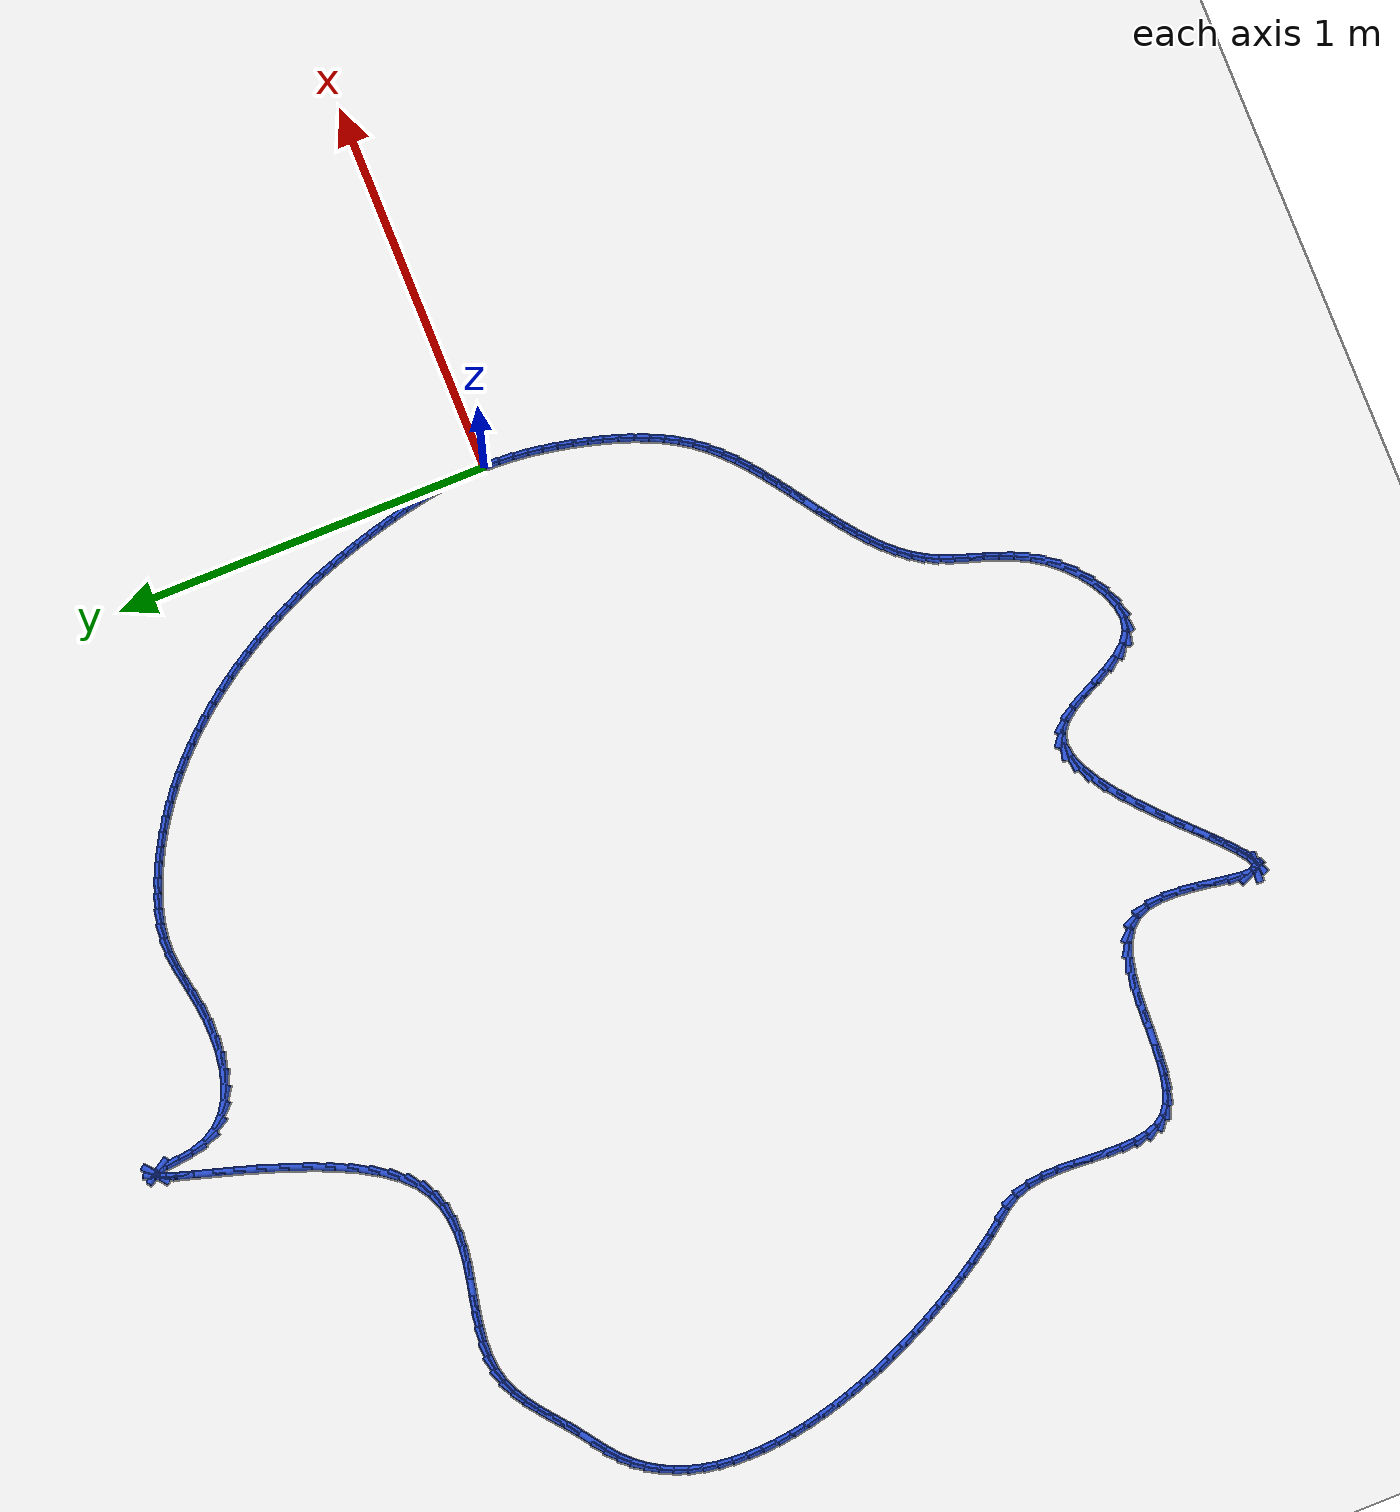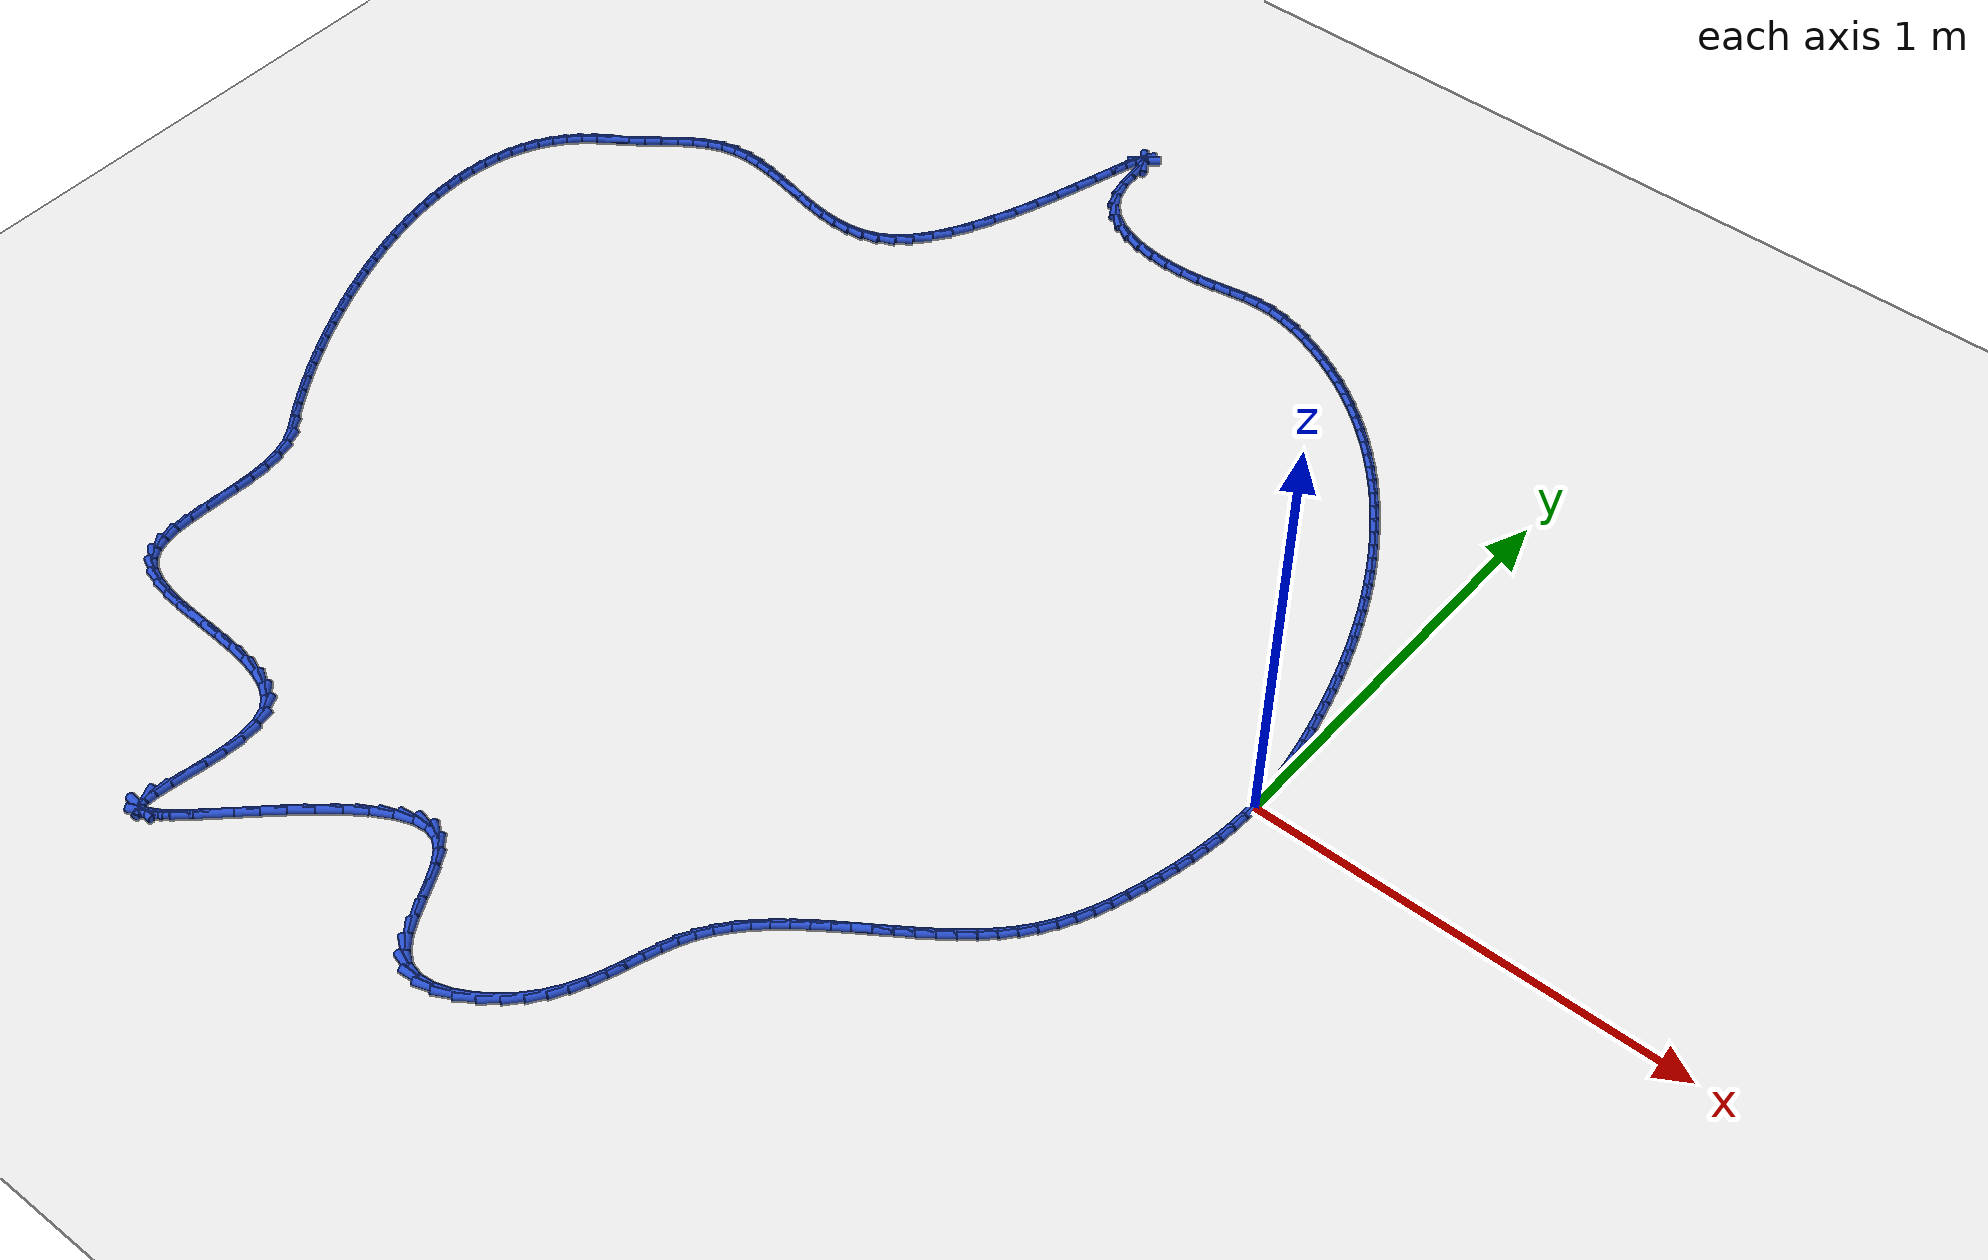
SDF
<sdf version="1.6">
 <world name="default">
  <light name="sun" type="directional">
   <pose>0 0 10 0 -0 0</pose>
   <diffuse>0.8 0.8 0.8 1</diffuse>
   <specular>0.2 0.2 0.2 1</specular>
   <attenuation>
    <range>1000</range>
    <constant>0.9</constant>
    <linear>0.01</linear>
    <quadratic>0.001</quadratic>
   </attenuation>
   <direction>-0.5 0.1 -0.9</direction>
  </light>
  <model name="ground_plane">
   <static>1</static>
   <link name="link">
    <collision name="collision">
     <geometry><plane><normal>0 0 1</normal><size>100 100</size></plane></geometry>
     <surface><friction><ode><mu>100</mu><mu2>50</mu2></ode></friction></surface>
    </collision>
    <visual name="visual">
     <cast_shadows>0</cast_shadows>
     <geometry><plane><normal>0 0 1</normal><size>100 100</size></plane></geometry>
     <material>
      <script><uri>file://media/materials/scripts/gazebo.material</uri><name>Gazebo/WhiteGlow</name></script>
     </material>
    </visual>
   </link>
  </model>
  <gravity>0 0 -9.8</gravity>
  <magnetic_field>6e-06 2.3e-05 -4.2e-05</magnetic_field>
  <atmosphere type="adiabatic"/>
  <physics name="default_physics" default="0" type="ode">
   <max_step_size>0.001</max_step_size>
   <real_time_factor>1</real_time_factor>
   <real_time_update_rate>1000</real_time_update_rate>
  </physics>
  <scene><ambient>0.4 0.4 0.4 1</ambient><background>0.7 0.7 0.7 1</background><shadows>1</shadows></scene>
  <spherical_coordinates>
   <surface_model>EARTH_WGS84</surface_model>
   <latitude_deg>0</latitude_deg>
   <longitude_deg>0</longitude_deg>
   <elevation>0</elevation>
   <heading_deg>0</heading_deg>
  </spherical_coordinates>
  <model name="line">
   <link name="link_0">
    <pose>-1.734723475976807e-18 -5.551115123125783e-17 0.01 0 1.57 -1.5428531095755291</pose>
    <collision name="collision">
     <geometry><cylinder><radius>0.01</radius><length>0.08</length></cylinder></geometry>
    </collision>
    <visual name="visual">
     <material>
      <script><name>Gazebo/Blue</name><uri>file://media/materials/scripts/gazebo.material</uri></script>
     </material>
     <geometry><cylinder><radius>0.01</radius><length>0.08</length></cylinder></geometry>
    </visual>
   </link>
   <link name="link_1">
    <pose>-0.0010769794216068187 0.03853167973899167 0.01 0 1.57 -1.4999491516372496</pose>
    <collision name="collision">
     <geometry><cylinder><radius>0.01</radius><length>0.08</length></cylinder></geometry>
    </collision>
    <visual name="visual">
     <material>
      <script><name>Gazebo/Blue</name><uri>file://media/materials/scripts/gazebo.material</uri></script>
     </material>
     <geometry><cylinder><radius>0.01</radius><length>0.08</length></cylinder></geometry>
    </visual>
   </link>
   <link name="link_2">
    <pose>-0.0038104905680952893 0.07705031017915327 0.01 0 1.57 -1.4612847658015455</pose>
    <collision name="collision">
     <geometry><cylinder><radius>0.01</radius><length>0.08</length></cylinder></geometry>
    </collision>
    <visual name="visual">
     <material>
      <script><name>Gazebo/Blue</name><uri>file://media/materials/scripts/gazebo.material</uri></script>
     </material>
     <geometry><cylinder><radius>0.01</radius><length>0.08</length></cylinder></geometry>
    </visual>
   </link>
   <link name="link_3">
    <pose>-0.008040696042351605 0.1155237029076431 0.01 0 1.57 -1.4268089031461204</pose>
    <collision name="collision">
     <geometry><cylinder><radius>0.01</radius><length>0.08</length></cylinder></geometry>
    </collision>
    <visual name="visual">
     <material>
      <script><name>Gazebo/Blue</name><uri>file://media/materials/scripts/gazebo.material</uri></script>
     </material>
     <geometry><cylinder><radius>0.01</radius><length>0.08</length></cylinder></geometry>
    </visual>
   </link>
   <link name="link_4">
    <pose>-0.013607758447261944 0.15391966951161945 0.01 0 1.57 -1.3964365449632792</pose>
    <collision name="collision">
     <geometry><cylinder><radius>0.01</radius><length>0.08</length></cylinder></geometry>
    </collision>
    <visual name="visual">
     <material>
      <script><name>Gazebo/Blue</name><uri>file://media/materials/scripts/gazebo.material</uri></script>
     </material>
     <geometry><cylinder><radius>0.01</radius><length>0.08</length></cylinder></geometry>
    </visual>
   </link>
   <link name="link_5">
    <pose>-0.020351840385712486 0.19220602157824074 0.01 0 1.57 -1.3700666504741452</pose>
    <collision name="collision">
     <geometry><cylinder><radius>0.01</radius><length>0.08</length></cylinder></geometry>
    </collision>
    <visual name="visual">
     <material>
      <script><name>Gazebo/Blue</name><uri>file://media/materials/scripts/gazebo.material</uri></script>
     </material>
     <geometry><cylinder><radius>0.01</radius><length>0.08</length></cylinder></geometry>
    </visual>
   </link>
   <link name="link_6">
    <pose>-0.028113104460589435 0.23035057069466533 0.01 0 1.57 -1.3475968002136869</pose>
    <collision name="collision">
     <geometry><cylinder><radius>0.01</radius><length>0.08</length></cylinder></geometry>
    </collision>
    <visual name="visual">
     <material>
      <script><name>Gazebo/Blue</name><uri>file://media/materials/scripts/gazebo.material</uri></script>
     </material>
     <geometry><cylinder><radius>0.01</radius><length>0.08</length></cylinder></geometry>
    </visual>
   </link>
   <link name="link_7">
    <pose>-0.036731713274778956 0.2683211284480515 0.01 0 1.57 -1.3282644170436997</pose>
    <collision name="collision">
     <geometry><cylinder><radius>0.01</radius><length>0.08</length></cylinder></geometry>
    </collision>
    <visual name="visual">
     <material>
      <script><name>Gazebo/Blue</name><uri>file://media/materials/scripts/gazebo.material</uri></script>
     </material>
     <geometry><cylinder><radius>0.01</radius><length>0.08</length></cylinder></geometry>
    </visual>
   </link>
   <link name="link_8">
    <pose>-0.046075174904024595 0.3060874564566931 0.01 0 1.57 -1.309001900247057</pose>
    <collision name="collision">
     <geometry><cylinder><radius>0.01</radius><length>0.08</length></cylinder></geometry>
    </collision>
    <visual name="visual">
     <material>
      <script><name>Gazebo/Blue</name><uri>file://media/materials/scripts/gazebo.material</uri></script>
     </material>
     <geometry><cylinder><radius>0.01</radius><length>0.08</length></cylinder></geometry>
    </visual>
   </link>
   <link name="link_9">
    <pose>-0.056133956291575575 0.34362808465023437 0.01 0 1.57 -1.2889520934286058</pose>
    <collision name="collision">
     <geometry><cylinder><radius>0.01</radius><length>0.08</length></cylinder></geometry>
    </collision>
    <visual name="visual">
     <material>
      <script><name>Gazebo/Blue</name><uri>file://media/materials/scripts/gazebo.material</uri></script>
     </material>
     <geometry><cylinder><radius>0.01</radius><length>0.08</length></cylinder></geometry>
    </visual>
   </link>
   <link name="link_10">
    <pose>-0.06693306934498469 0.38092400639189467 0.01 0 1.57 -1.2681109066922311</pose>
    <collision name="collision">
     <geometry><cylinder><radius>0.01</radius><length>0.08</length></cylinder></geometry>
    </collision>
    <visual name="visual">
     <material>
      <script><name>Gazebo/Blue</name><uri>file://media/materials/scripts/gazebo.material</uri></script>
     </material>
     <geometry><cylinder><radius>0.01</radius><length>0.08</length></cylinder></geometry>
    </visual>
   </link>
   <link name="link_11">
    <pose>-0.07849752779473321 0.41795621517488846 0.01 0 1.57 -1.2464768141689995</pose>
    <collision name="collision">
     <geometry><cylinder><radius>0.01</radius><length>0.08</length></cylinder></geometry>
    </collision>
    <visual name="visual">
     <material>
      <script><name>Gazebo/Blue</name><uri>file://media/materials/scripts/gazebo.material</uri></script>
     </material>
     <geometry><cylinder><radius>0.01</radius><length>0.08</length></cylinder></geometry>
    </visual>
   </link>
   <link name="link_12">
    <pose>-0.09085234537130234 0.45470570449242975 0.01 0 1.57 -1.2240512157923236</pose>
    <collision name="collision">
     <geometry><cylinder><radius>0.01</radius><length>0.08</length></cylinder></geometry>
    </collision>
    <visual name="visual">
     <material>
      <script><name>Gazebo/Blue</name><uri>file://media/materials/scripts/gazebo.material</uri></script>
     </material>
     <geometry><cylinder><radius>0.01</radius><length>0.08</length></cylinder></geometry>
    </visual>
   </link>
   <link name="link_13">
    <pose>-0.10402253580517332 0.49115346783773256 0.01 0 1.57 -1.200838851809362</pose>
    <collision name="collision">
     <geometry><cylinder><radius>0.01</radius><length>0.08</length></cylinder></geometry>
    </collision>
    <visual name="visual">
     <material>
      <script><name>Gazebo/Blue</name><uri>file://media/materials/scripts/gazebo.material</uri></script>
     </material>
     <geometry><cylinder><radius>0.01</radius><length>0.08</length></cylinder></geometry>
    </visual>
   </link>
   <link name="link_14">
    <pose>-0.11803311282682744 0.5272804987040115 0.01 0 1.57 -1.1768482164903336</pose>
    <collision name="collision">
     <geometry><cylinder><radius>0.01</radius><length>0.08</length></cylinder></geometry>
    </collision>
    <visual name="visual">
     <material>
      <script><name>Gazebo/Blue</name><uri>file://media/materials/scripts/gazebo.material</uri></script>
     </material>
     <geometry><cylinder><radius>0.01</radius><length>0.08</length></cylinder></geometry>
    </visual>
   </link>
   <link name="link_15">
    <pose>-0.13290909016674587 0.5630677905844803 0.01 0 1.57 -1.1520919601910362</pose>
    <collision name="collision">
     <geometry><cylinder><radius>0.01</radius><length>0.08</length></cylinder></geometry>
    </collision>
    <visual name="visual">
     <material>
      <script><name>Gazebo/Blue</name><uri>file://media/materials/scripts/gazebo.material</uri></script>
     </material>
     <geometry><cylinder><radius>0.01</radius><length>0.08</length></cylinder></geometry>
    </visual>
   </link>
   <link name="link_16">
    <pose>-0.14867548155540994 0.5984963369723536 0.01 0 1.57 -1.1265872670047505</pose>
    <collision name="collision">
     <geometry><cylinder><radius>0.01</radius><length>0.08</length></cylinder></geometry>
    </collision>
    <visual name="visual">
     <material>
      <script><name>Gazebo/Blue</name><uri>file://media/materials/scripts/gazebo.material</uri></script>
     </material>
     <geometry><cylinder><radius>0.01</radius><length>0.08</length></cylinder></geometry>
    </visual>
   </link>
   <link name="link_17">
    <pose>-0.1653573007233008 0.6335471313608452 0.01 0 1.57 -1.1003561935403843</pose>
    <collision name="collision">
     <geometry><cylinder><radius>0.01</radius><length>0.08</length></cylinder></geometry>
    </collision>
    <visual name="visual">
     <material>
      <script><name>Gazebo/Blue</name><uri>file://media/materials/scripts/gazebo.material</uri></script>
     </material>
     <geometry><cylinder><radius>0.01</radius><length>0.08</length></cylinder></geometry>
    </visual>
   </link>
   <link name="link_18">
    <pose>-0.1829795614008998 0.6682011672431697 0.01 0 1.57 -1.0734259530608419</pose>
    <collision name="collision">
     <geometry><cylinder><radius>0.01</radius><length>0.08</length></cylinder></geometry>
    </collision>
    <visual name="visual">
     <material>
      <script><name>Gazebo/Blue</name><uri>file://media/materials/scripts/gazebo.material</uri></script>
     </material>
     <geometry><cylinder><radius>0.01</radius><length>0.08</length></cylinder></geometry>
    </visual>
   </link>
   <link name="link_19">
    <pose>-0.20156727731868795 0.7024394381125406 0.01 0 1.57 -1.0458291172690408</pose>
    <collision name="collision">
     <geometry><cylinder><radius>0.01</radius><length>0.08</length></cylinder></geometry>
    </collision>
    <visual name="visual">
     <material>
      <script><name>Gazebo/Blue</name><uri>file://media/materials/scripts/gazebo.material</uri></script>
     </material>
     <geometry><cylinder><radius>0.01</radius><length>0.08</length></cylinder></geometry>
    </visual>
   </link>
   <link name="link_20">
    <pose>-0.22114546114582515 0.7362429347539926 0.01 0 1.57 -1.0175429551043644</pose>
    <collision name="collision">
     <geometry><cylinder><radius>0.01</radius><length>0.08</length></cylinder></geometry>
    </collision>
    <visual name="visual">
     <material>
      <script><name>Gazebo/Blue</name><uri>file://media/materials/scripts/gazebo.material</uri></script>
     </material>
     <geometry><cylinder><radius>0.01</radius><length>0.08</length></cylinder></geometry>
    </visual>
   </link>
   <link name="link_21">
    <pose>-0.24173426178577664 0.7695802370544793 0.01 0 1.57 -0.9883506114164637</pose>
    <collision name="collision">
     <geometry><cylinder><radius>0.01</radius><length>0.08</length></cylinder></geometry>
    </collision>
    <visual name="visual">
     <material>
      <script><name>Gazebo/Blue</name><uri>file://media/materials/scripts/gazebo.material</uri></script>
     </material>
     <geometry><cylinder><radius>0.01</radius><length>0.08</length></cylinder></geometry>
    </visual>
   </link>
   <link name="link_22">
    <pose>-0.2633377608457779 0.8023789258914512 0.01 0 1.57 -0.958122443582398</pose>
    <collision name="collision">
     <geometry><cylinder><radius>0.01</radius><length>0.08</length></cylinder></geometry>
    </collision>
    <visual name="visual">
     <material>
      <script><name>Gazebo/Blue</name><uri>file://media/materials/scripts/gazebo.material</uri></script>
     </material>
     <geometry><cylinder><radius>0.01</radius><length>0.08</length></cylinder></geometry>
    </visual>
   </link>
   <link name="link_23">
    <pose>-0.28595672673464445 0.8345581278354499 0.01 0 1.57 -0.9267653982786357</pose>
    <collision name="collision">
     <geometry><cylinder><radius>0.01</radius><length>0.08</length></cylinder></geometry>
    </collision>
    <visual name="visual">
     <material>
      <script><name>Gazebo/Blue</name><uri>file://media/materials/scripts/gazebo.material</uri></script>
     </material>
     <geometry><cylinder><radius>0.01</radius><length>0.08</length></cylinder></geometry>
    </visual>
   </link>
   <link name="link_24">
    <pose>-0.30959192786119155 0.8660369694570168 0.01 0 1.57 -0.8941886741220024</pose>
    <collision name="collision">
     <geometry><cylinder><radius>0.01</radius><length>0.08</length></cylinder></geometry>
    </collision>
    <visual name="visual">
     <material>
      <script><name>Gazebo/Blue</name><uri>file://media/materials/scripts/gazebo.material</uri></script>
     </material>
     <geometry><cylinder><radius>0.01</radius><length>0.08</length></cylinder></geometry>
    </visual>
   </link>
   <link name="link_25">
    <pose>-0.3342441326342345 0.8967345773266937 0.01 0 1.57 -0.8603048248830925</pose>
    <collision name="collision">
     <geometry><cylinder><radius>0.01</radius><length>0.08</length></cylinder></geometry>
    </collision>
    <visual name="visual">
     <material>
      <script><name>Gazebo/Blue</name><uri>file://media/materials/scripts/gazebo.material</uri></script>
     </material>
     <geometry><cylinder><radius>0.01</radius><length>0.08</length></cylinder></geometry>
    </visual>
   </link>
   <link name="link_26">
    <pose>-0.35991410946258917 0.9265700780150227 0.01 0 1.57 -0.8250312606817714</pose>
    <collision name="collision">
     <geometry><cylinder><radius>0.01</radius><length>0.08</length></cylinder></geometry>
    </collision>
    <visual name="visual">
     <material>
      <script><name>Gazebo/Blue</name><uri>file://media/materials/scripts/gazebo.material</uri></script>
     </material>
     <geometry><cylinder><radius>0.01</radius><length>0.08</length></cylinder></geometry>
    </visual>
   </link>
   <link name="link_27">
    <pose>-0.3866026267550707 0.9554625980925454 0.01 0 1.57 -0.7882921823689462</pose>
    <collision name="collision">
     <geometry><cylinder><radius>0.01</radius><length>0.08</length></cylinder></geometry>
    </collision>
    <visual name="visual">
     <material>
      <script><name>Gazebo/Blue</name><uri>file://media/materials/scripts/gazebo.material</uri></script>
     </material>
     <geometry><cylinder><radius>0.01</radius><length>0.08</length></cylinder></geometry>
    </visual>
   </link>
   <link name="link_28">
    <pose>-0.4143104529204943 0.983331264129803 0.01 0 1.57 -0.7500209726348099</pose>
    <collision name="collision">
     <geometry><cylinder><radius>0.01</radius><length>0.08</length></cylinder></geometry>
    </collision>
    <visual name="visual">
     <material>
      <script><name>Gazebo/Blue</name><uri>file://media/materials/scripts/gazebo.material</uri></script>
     </material>
     <geometry><cylinder><radius>0.01</radius><length>0.08</length></cylinder></geometry>
    </visual>
   </link>
   <link name="link_29">
    <pose>-0.44303835636767575 1.0100952026973378 0.01 0 1.57 -0.7101630459594466</pose>
    <collision name="collision">
     <geometry><cylinder><radius>0.01</radius><length>0.08</length></cylinder></geometry>
    </collision>
    <visual name="visual">
     <material>
      <script><name>Gazebo/Blue</name><uri>file://media/materials/scripts/gazebo.material</uri></script>
     </material>
     <geometry><cylinder><radius>0.01</radius><length>0.08</length></cylinder></geometry>
    </visual>
   </link>
   <link name="link_30">
    <pose>-0.4727871055054301 1.0356735403656914 0.01 0 1.57 -0.6686791260789898</pose>
    <collision name="collision">
     <geometry><cylinder><radius>0.01</radius><length>0.08</length></cylinder></geometry>
    </collision>
    <visual name="visual">
     <material>
      <script><name>Gazebo/Blue</name><uri>file://media/materials/scripts/gazebo.material</uri></script>
     </material>
     <geometry><cylinder><radius>0.01</radius><length>0.08</length></cylinder></geometry>
    </visual>
   </link>
   <link name="link_31">
    <pose>-0.503557468742573 1.059985403705405 0.01 0 1.57 -0.6255488726471353</pose>
    <collision name="collision">
     <geometry><cylinder><radius>0.01</radius><length>0.08</length></cylinder></geometry>
    </collision>
    <visual name="visual">
     <material>
      <script><name>Gazebo/Blue</name><uri>file://media/materials/scripts/gazebo.material</uri></script>
     </material>
     <geometry><cylinder><radius>0.01</radius><length>0.08</length></cylinder></geometry>
    </visual>
   </link>
   <link name="link_32">
    <pose>-0.5353502144879201 1.0829499192870213 0.01 0 1.57 -0.5807747183407559</pose>
    <collision name="collision">
     <geometry><cylinder><radius>0.01</radius><length>0.08</length></cylinder></geometry>
    </collision>
    <visual name="visual">
     <material>
      <script><name>Gazebo/Blue</name><uri>file://media/materials/scripts/gazebo.material</uri></script>
     </material>
     <geometry><cylinder><radius>0.01</radius><length>0.08</length></cylinder></geometry>
    </visual>
   </link>
   <link name="link_33">
    <pose>-0.568166111150286 1.104486213681081 0.01 0 1.57 -0.5343857066914498</pose>
    <collision name="collision">
     <geometry><cylinder><radius>0.01</radius><length>0.08</length></cylinder></geometry>
    </collision>
    <visual name="visual">
     <material>
      <script><name>Gazebo/Blue</name><uri>file://media/materials/scripts/gazebo.material</uri></script>
     </material>
     <geometry><cylinder><radius>0.01</radius><length>0.08</length></cylinder></geometry>
    </visual>
   </link>
   <link name="link_34">
    <pose>-0.602005927138487 1.1245134134581265 0.01 0 1.57 -0.4864410462582112</pose>
    <collision name="collision">
     <geometry><cylinder><radius>0.01</radius><length>0.08</length></cylinder></geometry>
    </collision>
    <visual name="visual">
     <material>
      <script><name>Gazebo/Blue</name><uri>file://media/materials/scripts/gazebo.material</uri></script>
     </material>
     <geometry><cylinder><radius>0.01</radius><length>0.08</length></cylinder></geometry>
    </visual>
   </link>
   <link name="link_35">
    <pose>-0.636870430861338 1.142950645188699 0.01 0 1.57 -0.4370330298851326</pose>
    <collision name="collision">
     <geometry><cylinder><radius>0.01</radius><length>0.08</length></cylinder></geometry>
    </collision>
    <visual name="visual">
     <material>
      <script><name>Gazebo/Blue</name><uri>file://media/materials/scripts/gazebo.material</uri></script>
     </material>
     <geometry><cylinder><radius>0.01</radius><length>0.08</length></cylinder></geometry>
    </visual>
   </link>
   <link name="link_36">
    <pose>-0.6727603907276547 1.1597170354433408 0.01 0 1.57 -0.38467385529505305</pose>
    <collision name="collision">
     <geometry><cylinder><radius>0.01</radius><length>0.08</length></cylinder></geometry>
    </collision>
    <visual name="visual">
     <material>
      <script><name>Gazebo/Blue</name><uri>file://media/materials/scripts/gazebo.material</uri></script>
     </material>
     <geometry><cylinder><radius>0.01</radius><length>0.08</length></cylinder></geometry>
    </visual>
   </link>
   <link name="link_37">
    <pose>-0.7096202934615161 1.1746394860055336 0.01 0 1.57 -0.32219894932615695</pose>
    <collision name="collision">
     <geometry><cylinder><radius>0.01</radius><length>0.08</length></cylinder></geometry>
    </collision>
    <visual name="visual">
     <material>
      <script><name>Gazebo/Blue</name><uri>file://media/materials/scripts/gazebo.material</uri></script>
     </material>
     <geometry><cylinder><radius>0.01</radius><length>0.08</length></cylinder></geometry>
    </visual>
   </link>
   <link name="link_38">
    <pose>-0.7471684251585913 1.1871742398043603 0.01 0 1.57 -0.24586596725841517</pose>
    <collision name="collision">
     <geometry><cylinder><radius>0.01</radius><length>0.08</length></cylinder></geometry>
    </collision>
    <visual name="visual">
     <material>
      <script><name>Gazebo/Blue</name><uri>file://media/materials/scripts/gazebo.material</uri></script>
     </material>
     <geometry><cylinder><radius>0.01</radius><length>0.08</length></cylinder></geometry>
    </visual>
   </link>
   <link name="link_39">
    <pose>-0.7850662520056675 1.196684433032282 0.01 0 1.57 -0.15307749985030616</pose>
    <collision name="collision">
     <geometry><cylinder><radius>0.01</radius><length>0.08</length></cylinder></geometry>
    </collision>
    <visual name="visual">
     <material>
      <script><name>Gazebo/Blue</name><uri>file://media/materials/scripts/gazebo.material</uri></script>
     </material>
     <geometry><cylinder><radius>0.01</radius><length>0.08</length></cylinder></geometry>
    </visual>
   </link>
   <link name="link_40">
    <pose>-0.8229752401893061 1.2025332018813897 0.01 0 1.57 -0.04130892806766804</pose>
    <collision name="collision">
     <geometry><cylinder><radius>0.01</radius><length>0.08</length></cylinder></geometry>
    </collision>
    <visual name="visual">
     <material>
      <script><name>Gazebo/Blue</name><uri>file://media/materials/scripts/gazebo.material</uri></script>
     </material>
     <geometry><cylinder><radius>0.01</radius><length>0.08</length></cylinder></geometry>
    </visual>
   </link>
   <link name="link_41">
    <pose>-0.8605581085588231 1.2040865935714296 0.01 0 1.57 0.073478094659854</pose>
    <collision name="collision">
     <geometry><cylinder><radius>0.01</radius><length>0.08</length></cylinder></geometry>
    </collision>
    <visual name="visual">
     <material>
      <script><name>Gazebo/Blue</name><uri>file://media/materials/scripts/gazebo.material</uri></script>
     </material>
     <geometry><cylinder><radius>0.01</radius><length>0.08</length></cylinder></geometry>
    </visual>
   </link>
   <link name="link_42">
    <pose>-0.89775214458735 1.2013487176050712 0.01 0 1.57 0.14855175083175318</pose>
    <collision name="collision">
     <geometry><cylinder><radius>0.01</radius><length>0.08</length></cylinder></geometry>
    </collision>
    <visual name="visual">
     <material>
      <script><name>Gazebo/Blue</name><uri>file://media/materials/scripts/gazebo.material</uri></script>
     </material>
     <geometry><cylinder><radius>0.01</radius><length>0.08</length></cylinder></geometry>
    </visual>
   </link>
   <link name="link_43">
    <pose>-0.9351117166173636 1.1957577003175448 0.01 0 1.57 0.17659292537964288</pose>
    <collision name="collision">
     <geometry><cylinder><radius>0.01</radius><length>0.08</length></cylinder></geometry>
    </collision>
    <visual name="visual">
     <material>
      <script><name>Gazebo/Blue</name><uri>file://media/materials/scripts/gazebo.material</uri></script>
     </material>
     <geometry><cylinder><radius>0.01</radius><length>0.08</length></cylinder></geometry>
    </visual>
   </link>
   <link name="link_44">
    <pose>-0.9732753871516355 1.1889473244791848 0.01 0 1.57 0.16010588954540345</pose>
    <collision name="collision">
     <geometry><cylinder><radius>0.01</radius><length>0.08</length></cylinder></geometry>
    </collision>
    <visual name="visual">
     <material>
      <script><name>Gazebo/Blue</name><uri>file://media/materials/scripts/gazebo.material</uri></script>
     </material>
     <geometry><cylinder><radius>0.01</radius><length>0.08</length></cylinder></geometry>
    </visual>
   </link>
   <link name="link_45">
    <pose>-1.0128817186929389 1.182551372860326 0.01 0 1.57 0.10472986271798332</pose>
    <collision name="collision">
     <geometry><cylinder><radius>0.01</radius><length>0.08</length></cylinder></geometry>
    </collision>
    <visual name="visual">
     <material>
      <script><name>Gazebo/Blue</name><uri>file://media/materials/scripts/gazebo.material</uri></script>
     </material>
     <geometry><cylinder><radius>0.01</radius><length>0.08</length></cylinder></geometry>
    </visual>
   </link>
   <link name="link_46">
    <pose>-1.0545206165256484 1.1781745228273068 0.01 0 1.57 0.03050445162533826</pose>
    <collision name="collision">
     <geometry><cylinder><radius>0.01</radius><length>0.08</length></cylinder></geometry>
    </collision>
    <visual name="visual">
     <material>
      <script><name>Gazebo/Blue</name><uri>file://media/materials/scripts/gazebo.material</uri></script>
     </material>
     <geometry><cylinder><radius>0.01</radius><length>0.08</length></cylinder></geometry>
    </visual>
   </link>
   <link name="link_47">
    <pose>-1.097831564921569 1.1768529361500482 0.01 0 1.57 -0.051427261396491196</pose>
    <collision name="collision">
     <geometry><cylinder><radius>0.01</radius><length>0.08</length></cylinder></geometry>
    </collision>
    <visual name="visual">
     <material>
      <script><name>Gazebo/Blue</name><uri>file://media/materials/scripts/gazebo.material</uri></script>
     </material>
     <geometry><cylinder><radius>0.01</radius><length>0.08</length></cylinder></geometry>
    </visual>
   </link>
   <link name="link_48">
    <pose>-1.1415888545327935 1.1791052396742412 0.01 0 1.57 -0.14624697940876588</pose>
    <collision name="collision">
     <geometry><cylinder><radius>0.01</radius><length>0.08</length></cylinder></geometry>
    </collision>
    <visual name="visual">
     <material>
      <script><name>Gazebo/Blue</name><uri>file://media/materials/scripts/gazebo.material</uri></script>
     </material>
     <geometry><cylinder><radius>0.01</radius><length>0.08</length></cylinder></geometry>
    </visual>
   </link>
   <link name="link_49">
    <pose>-1.1845352114513992 1.1854311791976786 0.01 0 1.57 -0.26056770459491707</pose>
    <collision name="collision">
     <geometry><cylinder><radius>0.01</radius><length>0.08</length></cylinder></geometry>
    </collision>
    <visual name="visual">
     <material>
      <script><name>Gazebo/Blue</name><uri>file://media/materials/scripts/gazebo.material</uri></script>
     </material>
     <geometry><cylinder><radius>0.01</radius><length>0.08</length></cylinder></geometry>
    </visual>
   </link>
   <link name="link_50">
    <pose>-1.2254133617694656 1.1963305005181528 0.01 0 1.57 -0.4021540027335433</pose>
    <collision name="collision">
     <geometry><cylinder><radius>0.01</radius><length>0.08</length></cylinder></geometry>
    </collision>
    <visual name="visual">
     <material>
      <script><name>Gazebo/Blue</name><uri>file://media/materials/scripts/gazebo.material</uri></script>
     </material>
     <geometry><cylinder><radius>0.01</radius><length>0.08</length></cylinder></geometry>
    </visual>
   </link>
   <link name="link_51">
    <pose>-1.2629660315790712 1.2123029494334576 0.01 0 1.57 -0.5788207469783011</pose>
    <collision name="collision">
     <geometry><cylinder><radius>0.01</radius><length>0.08</length></cylinder></geometry>
    </collision>
    <visual name="visual">
     <material>
      <script><name>Gazebo/Blue</name><uri>file://media/materials/scripts/gazebo.material</uri></script>
     </material>
     <geometry><cylinder><radius>0.01</radius><length>0.08</length></cylinder></geometry>
    </visual>
   </link>
   <link name="link_52">
    <pose>-1.295935946972294 1.2338482717413843 0.01 0 1.57 -0.7943125169757361</pose>
    <collision name="collision">
     <geometry><cylinder><radius>0.01</radius><length>0.08</length></cylinder></geometry>
    </collision>
    <visual name="visual">
     <material>
      <script><name>Gazebo/Blue</name><uri>file://media/materials/scripts/gazebo.material</uri></script>
     </material>
     <geometry><cylinder><radius>0.01</radius><length>0.08</length></cylinder></geometry>
    </visual>
   </link>
   <link name="link_53">
    <pose>-1.3230658340412136 1.2614662132397267 0.01 0 1.57 -1.0407984475117928</pose>
    <collision name="collision">
     <geometry><cylinder><radius>0.01</radius><length>0.08</length></cylinder></geometry>
    </collision>
    <visual name="visual">
     <material>
      <script><name>Gazebo/Blue</name><uri>file://media/materials/scripts/gazebo.material</uri></script>
     </material>
     <geometry><cylinder><radius>0.01</radius><length>0.08</length></cylinder></geometry>
    </visual>
   </link>
   <link name="link_54">
    <pose>-1.3430984188779078 1.2956565197262773 0.01 0 1.57 -1.2797417583829147</pose>
    <collision name="collision">
     <geometry><cylinder><radius>0.01</radius><length>0.08</length></cylinder></geometry>
    </collision>
    <visual name="visual">
     <material>
      <script><name>Gazebo/Blue</name><uri>file://media/materials/scripts/gazebo.material</uri></script>
     </material>
     <geometry><cylinder><radius>0.01</radius><length>0.08</length></cylinder></geometry>
    </visual>
   </link>
   <link name="link_55">
    <pose>-1.3552226402459078 1.3361297322374697 0.01 0 1.57 -1.4208867539696892</pose>
    <collision name="collision">
     <geometry><cylinder><radius>0.01</radius><length>0.08</length></cylinder></geometry>
    </collision>
    <visual name="visual">
     <material>
      <script><name>Gazebo/Blue</name><uri>file://media/materials/scripts/gazebo.material</uri></script>
     </material>
     <geometry><cylinder><radius>0.01</radius><length>0.08</length></cylinder></geometry>
    </visual>
   </link>
   <link name="link_56">
    <pose>-1.361479244165218 1.3775524743925938 0.01 0 1.57 -1.469807228665049</pose>
    <collision name="collision">
     <geometry><cylinder><radius>0.01</radius><length>0.08</length></cylinder></geometry>
    </collision>
    <visual name="visual">
     <material>
      <script><name>Gazebo/Blue</name><uri>file://media/materials/scripts/gazebo.material</uri></script>
     </material>
     <geometry><cylinder><radius>0.01</radius><length>0.08</length></cylinder></geometry>
    </visual>
   </link>
   <link name="link_57">
    <pose>-1.365031373855405 1.4126062150390049 0.01 0 1.57 -1.4000625566689096</pose>
    <collision name="collision">
     <geometry><cylinder><radius>0.01</radius><length>0.08</length></cylinder></geometry>
    </collision>
    <visual name="visual">
     <material>
      <script><name>Gazebo/Blue</name><uri>file://media/materials/scripts/gazebo.material</uri></script>
     </material>
     <geometry><cylinder><radius>0.01</radius><length>0.08</length></cylinder></geometry>
    </visual>
   </link>
   <link name="link_58">
    <pose>-1.368822848540975 1.4345969575189295 0.01 0 1.57 -0.98458259522996</pose>
    <collision name="collision">
     <geometry><cylinder><radius>0.01</radius><length>0.08</length></cylinder></geometry>
    </collision>
    <visual name="visual">
     <material>
      <script><name>Gazebo/Blue</name><uri>file://media/materials/scripts/gazebo.material</uri></script>
     </material>
     <geometry><cylinder><radius>0.01</radius><length>0.08</length></cylinder></geometry>
    </visual>
   </link>
   <link name="link_59">
    <pose>-1.3738923343924123 1.4422307387749302 0.01 0 1.57 0.687512411817933</pose>
    <collision name="collision">
     <geometry><cylinder><radius>0.01</radius><length>0.08</length></cylinder></geometry>
    </collision>
    <visual name="visual">
     <material>
      <script><name>Gazebo/Blue</name><uri>file://media/materials/scripts/gazebo.material</uri></script>
     </material>
     <geometry><cylinder><radius>0.01</radius><length>0.08</length></cylinder></geometry>
    </visual>
   </link>
   <link name="link_60">
    <pose>-1.3803089806841495 1.4369616289344793 0.01 0 1.57 1.1325113725217084</pose>
    <collision name="collision">
     <geometry><cylinder><radius>0.01</radius><length>0.08</length></cylinder></geometry>
    </collision>
    <visual name="visual">
     <material>
      <script><name>Gazebo/Blue</name><uri>file://media/materials/scripts/gazebo.material</uri></script>
     </material>
     <geometry><cylinder><radius>0.01</radius><length>0.08</length></cylinder></geometry>
    </visual>
   </link>
   <link name="link_61">
    <pose>-1.388134259178518 1.4202654595385038 0.01 0 1.57 1.2351651799047005</pose>
    <collision name="collision">
     <geometry><cylinder><radius>0.01</radius><length>0.08</length></cylinder></geometry>
    </collision>
    <visual name="visual">
     <material>
      <script><name>Gazebo/Blue</name><uri>file://media/materials/scripts/gazebo.material</uri></script>
     </material>
     <geometry><cylinder><radius>0.01</radius><length>0.08</length></cylinder></geometry>
    </visual>
   </link>
   <link name="link_62">
    <pose>-1.3974296416378493 1.3936180621279333 0.01 0 1.57 1.2717787340528484</pose>
    <collision name="collision">
     <geometry><cylinder><radius>0.01</radius><length>0.08</length></cylinder></geometry>
    </collision>
    <visual name="visual">
     <material>
      <script><name>Gazebo/Blue</name><uri>file://media/materials/scripts/gazebo.material</uri></script>
     </material>
     <geometry><cylinder><radius>0.01</radius><length>0.08</length></cylinder></geometry>
    </visual>
   </link>
   <link name="link_63">
    <pose>-1.4082565998244754 1.358495268243697 0.01 0 1.57 1.2840659904218539</pose>
    <collision name="collision">
     <geometry><cylinder><radius>0.01</radius><length>0.08</length></cylinder></geometry>
    </collision>
    <visual name="visual">
     <material>
      <script><name>Gazebo/Blue</name><uri>file://media/materials/scripts/gazebo.material</uri></script>
     </material>
     <geometry><cylinder><radius>0.01</radius><length>0.08</length></cylinder></geometry>
    </visual>
   </link>
   <link name="link_64">
    <pose>-1.4206766055007285 1.316372909426724 0.01 0 1.57 1.2835675635956658</pose>
    <collision name="collision">
     <geometry><cylinder><radius>0.01</radius><length>0.08</length></cylinder></geometry>
    </collision>
    <visual name="visual">
     <material>
      <script><name>Gazebo/Blue</name><uri>file://media/materials/scripts/gazebo.material</uri></script>
     </material>
     <geometry><cylinder><radius>0.01</radius><length>0.08</length></cylinder></geometry>
    </visual>
   </link>
   <link name="link_65">
    <pose>-1.4347511304289393 1.2687268172179424 0.01 0 1.57 1.2743367036474234</pose>
    <collision name="collision">
     <geometry><cylinder><radius>0.01</radius><length>0.08</length></cylinder></geometry>
    </collision>
    <visual name="visual">
     <material>
      <script><name>Gazebo/Blue</name><uri>file://media/materials/scripts/gazebo.material</uri></script>
     </material>
     <geometry><cylinder><radius>0.01</radius><length>0.08</length></cylinder></geometry>
    </visual>
   </link>
   <link name="link_66">
    <pose>-1.4505416463714398 1.2170328231582808 0.01 0 1.57 1.2577064272172573</pose>
    <collision name="collision">
     <geometry><cylinder><radius>0.01</radius><length>0.08</length></cylinder></geometry>
    </collision>
    <visual name="visual">
     <material>
      <script><name>Gazebo/Blue</name><uri>file://media/materials/scripts/gazebo.material</uri></script>
     </material>
     <geometry><cylinder><radius>0.01</radius><length>0.08</length></cylinder></geometry>
    </visual>
   </link>
   <link name="link_67">
    <pose>-1.4681096250905625 1.1627667587886703 0.01 0 1.57 1.233637116908888</pose>
    <collision name="collision">
     <geometry><cylinder><radius>0.01</radius><length>0.08</length></cylinder></geometry>
    </collision>
    <visual name="visual">
     <material>
      <script><name>Gazebo/Blue</name><uri>file://media/materials/scripts/gazebo.material</uri></script>
     </material>
     <geometry><cylinder><radius>0.01</radius><length>0.08</length></cylinder></geometry>
    </visual>
   </link>
   <link name="link_68">
    <pose>-1.4875165383486384 1.1074044556500373 0.01 0 1.57 1.201088013503214</pose>
    <collision name="collision">
     <geometry><cylinder><radius>0.01</radius><length>0.08</length></cylinder></geometry>
    </collision>
    <visual name="visual">
     <material>
      <script><name>Gazebo/Blue</name><uri>file://media/materials/scripts/gazebo.material</uri></script>
     </material>
     <geometry><cylinder><radius>0.01</radius><length>0.08</length></cylinder></geometry>
    </visual>
   </link>
   <link name="link_69">
    <pose>-1.508823857907999 1.0524217452833127 0.01 0 1.57 1.1579750342196502</pose>
    <collision name="collision">
     <geometry><cylinder><radius>0.01</radius><length>0.08</length></cylinder></geometry>
    </collision>
    <visual name="visual">
     <material>
      <script><name>Gazebo/Blue</name><uri>file://media/materials/scripts/gazebo.material</uri></script>
     </material>
     <geometry><cylinder><radius>0.01</radius><length>0.08</length></cylinder></geometry>
    </visual>
   </link>
   <link name="link_70">
    <pose>-1.5320930555309769 0.9992944592294232 0.01 0 1.57 1.1008304515854521</pose>
    <collision name="collision">
     <geometry><cylinder><radius>0.01</radius><length>0.08</length></cylinder></geometry>
    </collision>
    <visual name="visual">
     <material>
      <script><name>Gazebo/Blue</name><uri>file://media/materials/scripts/gazebo.material</uri></script>
     </material>
     <geometry><cylinder><radius>0.01</radius><length>0.08</length></cylinder></geometry>
    </visual>
   </link>
   <link name="link_71">
    <pose>-1.5573856029799031 0.9494984290293003 0.01 0 1.57 1.024124346306182</pose>
    <collision name="collision">
     <geometry><cylinder><radius>0.01</radius><length>0.08</length></cylinder></geometry>
    </collision>
    <visual name="visual">
     <material>
      <script><name>Gazebo/Blue</name><uri>file://media/materials/scripts/gazebo.material</uri></script>
     </material>
     <geometry><cylinder><radius>0.01</radius><length>0.08</length></cylinder></geometry>
    </visual>
   </link>
   <link name="link_72">
    <pose>-1.58476297201711 0.904509486223871 0.01 0 1.57 0.9191745342499368</pose>
    <collision name="collision">
     <geometry><cylinder><radius>0.01</radius><length>0.08</length></cylinder></geometry>
    </collision>
    <visual name="visual">
     <material>
      <script><name>Gazebo/Blue</name><uri>file://media/materials/scripts/gazebo.material</uri></script>
     </material>
     <geometry><cylinder><radius>0.01</radius><length>0.08</length></cylinder></geometry>
    </visual>
   </link>
   <link name="link_73">
    <pose>-1.614286634404928 0.8658034623540651 0.01 0 1.57 0.7729270895372587</pose>
    <collision name="collision">
     <geometry><cylinder><radius>0.01</radius><length>0.08</length></cylinder></geometry>
    </collision>
    <visual name="visual">
     <material>
      <script><name>Gazebo/Blue</name><uri>file://media/materials/scripts/gazebo.material</uri></script>
     </material>
     <geometry><cylinder><radius>0.01</radius><length>0.08</length></cylinder></geometry>
    </visual>
   </link>
   <link name="link_74">
    <pose>-1.6460177681856738 0.8348540626633555 0.01 0 1.57 0.5838277135060976</pose>
    <collision name="collision">
     <geometry><cylinder><radius>0.01</radius><length>0.08</length></cylinder></geometry>
    </collision>
    <visual name="visual">
     <material>
      <script><name>Gazebo/Blue</name><uri>file://media/materials/scripts/gazebo.material</uri></script>
     </material>
     <geometry><cylinder><radius>0.01</radius><length>0.08</length></cylinder></geometry>
    </visual>
   </link>
   <link name="link_75">
    <pose>-1.679923500570183 0.8124541397728001 0.01 0 1.57 0.3896519165907768</pose>
    <collision name="collision">
     <geometry><cylinder><radius>0.01</radius><length>0.08</length></cylinder></geometry>
    </collision>
    <visual name="visual">
     <material>
      <script><name>Gazebo/Blue</name><uri>file://media/materials/scripts/gazebo.material</uri></script>
     </material>
     <geometry><cylinder><radius>0.01</radius><length>0.08</length></cylinder></geometry>
    </visual>
   </link>
   <link name="link_76">
    <pose>-1.7157428200880442 0.7977450051425384 0.01 0 1.57 0.21364988575221486</pose>
    <collision name="collision">
     <geometry><cylinder><radius>0.01</radius><length>0.08</length></cylinder></geometry>
    </collision>
    <visual name="visual">
     <material>
      <script><name>Gazebo/Blue</name><uri>file://media/materials/scripts/gazebo.material</uri></script>
     </material>
     <geometry><cylinder><radius>0.01</radius><length>0.08</length></cylinder></geometry>
    </visual>
   </link>
   <link name="link_77">
    <pose>-1.7531807956816696 0.789622419613788 0.01 0 1.57 0.06801052286666809</pose>
    <collision name="collision">
     <geometry><cylinder><radius>0.01</radius><length>0.08</length></cylinder></geometry>
    </collision>
    <visual name="visual">
     <material>
      <script><name>Gazebo/Blue</name><uri>file://media/materials/scripts/gazebo.material</uri></script>
     </material>
     <geometry><cylinder><radius>0.01</radius><length>0.08</length></cylinder></geometry>
    </visual>
   </link>
   <link name="link_78">
    <pose>-1.791942496293471 0.7869821440277677 0.01 0 1.57 -0.0436458907449302</pose>
    <collision name="collision">
     <geometry><cylinder><radius>0.01</radius><length>0.08</length></cylinder></geometry>
    </collision>
    <visual name="visual">
     <material>
      <script><name>Gazebo/Blue</name><uri>file://media/materials/scripts/gazebo.material</uri></script>
     </material>
     <geometry><cylinder><radius>0.01</radius><length>0.08</length></cylinder></geometry>
    </visual>
   </link>
   <link name="link_79">
    <pose>-1.8317329908658608 0.7887199392256946 0.01 0 1.57 -0.12304474501848074</pose>
    <collision name="collision">
     <geometry><cylinder><radius>0.01</radius><length>0.08</length></cylinder></geometry>
    </collision>
    <visual name="visual">
     <material>
      <script><name>Gazebo/Blue</name><uri>file://media/materials/scripts/gazebo.material</uri></script>
     </material>
     <geometry><cylinder><radius>0.01</radius><length>0.08</length></cylinder></geometry>
    </visual>
   </link>
   <link name="link_80">
    <pose>-1.872257348341252 0.7937315660487878 0.01 0 1.57 -0.17354513725176587</pose>
    <collision name="collision">
     <geometry><cylinder><radius>0.01</radius><length>0.08</length></cylinder></geometry>
    </collision>
    <visual name="visual">
     <material>
      <script><name>Gazebo/Blue</name><uri>file://media/materials/scripts/gazebo.material</uri></script>
     </material>
     <geometry><cylinder><radius>0.01</radius><length>0.08</length></cylinder></geometry>
    </visual>
   </link>
   <link name="link_81">
    <pose>-1.913220637662056 0.8009127853382647 0.01 0 1.57 -0.19798294448163245</pose>
    <collision name="collision">
     <geometry><cylinder><radius>0.01</radius><length>0.08</length></cylinder></geometry>
    </collision>
    <visual name="visual">
     <material>
      <script><name>Gazebo/Blue</name><uri>file://media/materials/scripts/gazebo.material</uri></script>
     </material>
     <geometry><cylinder><radius>0.01</radius><length>0.08</length></cylinder></geometry>
    </visual>
   </link>
   <link name="link_82">
    <pose>-1.9543279277706853 0.8091593579353433 0.01 0 1.57 -0.1977809022821603</pose>
    <collision name="collision">
     <geometry><cylinder><radius>0.01</radius><length>0.08</length></cylinder></geometry>
    </collision>
    <visual name="visual">
     <material>
      <script><name>Gazebo/Blue</name><uri>file://media/materials/scripts/gazebo.material</uri></script>
     </material>
     <geometry><cylinder><radius>0.01</radius><length>0.08</length></cylinder></geometry>
    </visual>
   </link>
   <link name="link_83">
    <pose>-1.9952842876095525 0.8173670446812417 0.01 0 1.57 -0.17265219575376914</pose>
    <collision name="collision">
     <geometry><cylinder><radius>0.01</radius><length>0.08</length></cylinder></geometry>
    </collision>
    <visual name="visual">
     <material>
      <script><name>Gazebo/Blue</name><uri>file://media/materials/scripts/gazebo.material</uri></script>
     </material>
     <geometry><cylinder><radius>0.01</radius><length>0.08</length></cylinder></geometry>
    </visual>
   </link>
   <link name="link_84">
    <pose>-2.0357947861210692 0.8244316064171783 0.01 0 1.57 -0.12054008566198647</pose>
    <collision name="collision">
     <geometry><cylinder><radius>0.01</radius><length>0.08</length></cylinder></geometry>
    </collision>
    <visual name="visual">
     <material>
      <script><name>Gazebo/Blue</name><uri>file://media/materials/scripts/gazebo.material</uri></script>
     </material>
     <geometry><cylinder><radius>0.01</radius><length>0.08</length></cylinder></geometry>
    </visual>
   </link>
   <link name="link_85">
    <pose>-2.075564492247649 0.8292488039843706 0.01 0 1.57 -0.03781938551490787</pose>
    <collision name="collision">
     <geometry><cylinder><radius>0.01</radius><length>0.08</length></cylinder></geometry>
    </collision>
    <visual name="visual">
     <material>
      <script><name>Gazebo/Blue</name><uri>file://media/materials/scripts/gazebo.material</uri></script>
     </material>
     <geometry><cylinder><radius>0.01</radius><length>0.08</length></cylinder></geometry>
    </visual>
   </link>
   <link name="link_86">
    <pose>-2.1142984749317018 0.8307143982240368 0.01 0 1.57 0.07977637594943718</pose>
    <collision name="collision">
     <geometry><cylinder><radius>0.01</radius><length>0.08</length></cylinder></geometry>
    </collision>
    <visual name="visual">
     <material>
      <script><name>Gazebo/Blue</name><uri>file://media/materials/scripts/gazebo.material</uri></script>
     </material>
     <geometry><cylinder><radius>0.01</radius><length>0.08</length></cylinder></geometry>
    </visual>
   </link>
   <link name="link_87">
    <pose>-2.1517018031156425 0.8277241499773953 0.01 0 1.57 0.23438262253025982</pose>
    <collision name="collision">
     <geometry><cylinder><radius>0.01</radius><length>0.08</length></cylinder></geometry>
    </collision>
    <visual name="visual">
     <material>
      <script><name>Gazebo/Blue</name><uri>file://media/materials/scripts/gazebo.material</uri></script>
     </material>
     <geometry><cylinder><radius>0.01</radius><length>0.08</length></cylinder></geometry>
    </visual>
   </link>
   <link name="link_88">
    <pose>-2.18748161788283 0.8191809666712081 0.01 0 1.57 0.3999697519081523</pose>
    <collision name="collision">
     <geometry><cylinder><radius>0.01</radius><length>0.08</length></cylinder></geometry>
    </collision>
    <visual name="visual">
     <material>
      <script><name>Gazebo/Blue</name><uri>file://media/materials/scripts/gazebo.material</uri></script>
     </material>
     <geometry><cylinder><radius>0.01</radius><length>0.08</length></cylinder></geometry>
    </visual>
   </link>
   <link name="link_89">
    <pose>-2.221571626541716 0.80476915764935 0.01 0 1.57 0.5283141425727861</pose>
    <collision name="collision">
     <geometry><cylinder><radius>0.01</radius><length>0.08</length></cylinder></geometry>
    </collision>
    <visual name="visual">
     <material>
      <script><name>Gazebo/Blue</name><uri>file://media/materials/scripts/gazebo.material</uri></script>
     </material>
     <geometry><cylinder><radius>0.01</radius><length>0.08</length></cylinder></geometry>
    </visual>
   </link>
   <link name="link_90">
    <pose>-2.254333129726219 0.7856477544660716 0.01 0 1.57 0.615330156898499</pose>
    <collision name="collision">
     <geometry><cylinder><radius>0.01</radius><length>0.08</length></cylinder></geometry>
    </collision>
    <visual name="visual">
     <material>
      <script><name>Gazebo/Blue</name><uri>file://media/materials/scripts/gazebo.material</uri></script>
     </material>
     <geometry><cylinder><radius>0.01</radius><length>0.08</length></cylinder></geometry>
    </visual>
   </link>
   <link name="link_91">
    <pose>-2.2861748641199 0.7631393903780261 0.01 0 1.57 0.665094621866829</pose>
    <collision name="collision">
     <geometry><cylinder><radius>0.01</radius><length>0.08</length></cylinder></geometry>
    </collision>
    <visual name="visual">
     <material>
      <script><name>Gazebo/Blue</name><uri>file://media/materials/scripts/gazebo.material</uri></script>
     </material>
     <geometry><cylinder><radius>0.01</radius><length>0.08</length></cylinder></geometry>
    </visual>
   </link>
   <link name="link_92">
    <pose>-2.3175055664063224 0.7385666986418661 0.01 0 1.57 0.6811833779575613</pose>
    <collision name="collision">
     <geometry><cylinder><radius>0.01</radius><length>0.08</length></cylinder></geometry>
    </collision>
    <visual name="visual">
     <material>
      <script><name>Gazebo/Blue</name><uri>file://media/materials/scripts/gazebo.material</uri></script>
     </material>
     <geometry><cylinder><radius>0.01</radius><length>0.08</length></cylinder></geometry>
    </visual>
   </link>
   <link name="link_93">
    <pose>-2.3487339732690473 0.7132523125142439 0.01 0 1.57 0.6651072620050574</pose>
    <collision name="collision">
     <geometry><cylinder><radius>0.01</radius><length>0.08</length></cylinder></geometry>
    </collision>
    <visual name="visual">
     <material>
      <script><name>Gazebo/Blue</name><uri>file://media/materials/scripts/gazebo.material</uri></script>
     </material>
     <geometry><cylinder><radius>0.01</radius><length>0.08</length></cylinder></geometry>
    </visual>
   </link>
   <link name="link_94">
    <pose>-2.380268821391636 0.688518865251812 0.01 0 1.57 0.6261668625341004</pose>
    <collision name="collision">
     <geometry><cylinder><radius>0.01</radius><length>0.08</length></cylinder></geometry>
    </collision>
    <visual name="visual">
     <material>
      <script><name>Gazebo/Blue</name><uri>file://media/materials/scripts/gazebo.material</uri></script>
     </material>
     <geometry><cylinder><radius>0.01</radius><length>0.08</length></cylinder></geometry>
    </visual>
   </link>
   <link name="link_95">
    <pose>-2.4122917938123356 0.6653579238884731 0.01 0 1.57 0.626095446296929</pose>
    <collision name="collision">
     <geometry><cylinder><radius>0.01</radius><length>0.08</length></cylinder></geometry>
    </collision>
    <visual name="visual">
     <material>
      <script><name>Gazebo/Blue</name><uri>file://media/materials/scripts/gazebo.material</uri></script>
     </material>
     <geometry><cylinder><radius>0.01</radius><length>0.08</length></cylinder></geometry>
    </visual>
   </link>
   <link name="link_96">
    <pose>-2.4435886014168857 0.6427255927508299 0.01 0 1.57 0.6918697168758401</pose>
    <collision name="collision">
     <geometry><cylinder><radius>0.01</radius><length>0.08</length></cylinder></geometry>
    </collision>
    <visual name="visual">
     <material>
      <script><name>Gazebo/Blue</name><uri>file://media/materials/scripts/gazebo.material</uri></script>
     </material>
     <geometry><cylinder><radius>0.01</radius><length>0.08</length></cylinder></geometry>
    </visual>
   </link>
   <link name="link_97">
    <pose>-2.4724352960401896 0.6188265592326165 0.01 0 1.57 0.7988593255718446</pose>
    <collision name="collision">
     <geometry><cylinder><radius>0.01</radius><length>0.08</length></cylinder></geometry>
    </collision>
    <visual name="visual">
     <material>
      <script><name>Gazebo/Blue</name><uri>file://media/materials/scripts/gazebo.material</uri></script>
     </material>
     <geometry><cylinder><radius>0.01</radius><length>0.08</length></cylinder></geometry>
    </visual>
   </link>
   <link name="link_98">
    <pose>-2.4978841605324256 0.5926831609735262 0.01 0 1.57 0.9079831469648736</pose>
    <collision name="collision">
     <geometry><cylinder><radius>0.01</radius><length>0.08</length></cylinder></geometry>
    </collision>
    <visual name="visual">
     <material>
      <script><name>Gazebo/Blue</name><uri>file://media/materials/scripts/gazebo.material</uri></script>
     </material>
     <geometry><cylinder><radius>0.01</radius><length>0.08</length></cylinder></geometry>
    </visual>
   </link>
   <link name="link_99">
    <pose>-2.519985997748386 0.5643700666400359 0.01 0 1.57 1.01434771990306</pose>
    <collision name="collision">
     <geometry><cylinder><radius>0.01</radius><length>0.08</length></cylinder></geometry>
    </collision>
    <visual name="visual">
     <material>
      <script><name>Gazebo/Blue</name><uri>file://media/materials/scripts/gazebo.material</uri></script>
     </material>
     <geometry><cylinder><radius>0.01</radius><length>0.08</length></cylinder></geometry>
    </visual>
   </link>
   <link name="link_100">
    <pose>-2.5388572327230827 0.534031103509343 0.01 0 1.57 1.1159626708045105</pose>
    <collision name="collision">
     <geometry><cylinder><radius>0.01</radius><length>0.08</length></cylinder></geometry>
    </collision>
    <visual name="visual">
     <material>
      <script><name>Gazebo/Blue</name><uri>file://media/materials/scripts/gazebo.material</uri></script>
     </material>
     <geometry><cylinder><radius>0.01</radius><length>0.08</length></cylinder></geometry>
    </visual>
   </link>
   <link name="link_101">
    <pose>-2.554614290491531 0.5018100988586436 0.01 0 1.57 1.211390757309062</pose>
    <collision name="collision">
     <geometry><cylinder><radius>0.01</radius><length>0.08</length></cylinder></geometry>
    </collision>
    <visual name="visual">
     <material>
      <script><name>Gazebo/Blue</name><uri>file://media/materials/scripts/gazebo.material</uri></script>
     </material>
     <geometry><cylinder><radius>0.01</radius><length>0.08</length></cylinder></geometry>
    </visual>
   </link>
   <link name="link_102">
    <pose>-2.567373596088745 0.4678508799651356 0.01 0 1.57 1.299797858621396</pose>
    <collision name="collision">
     <geometry><cylinder><radius>0.01</radius><length>0.08</length></cylinder></geometry>
    </collision>
    <visual name="visual">
     <material>
      <script><name>Gazebo/Blue</name><uri>file://media/materials/scripts/gazebo.material</uri></script>
     </material>
     <geometry><cylinder><radius>0.01</radius><length>0.08</length></cylinder></geometry>
    </visual>
   </link>
   <link name="link_103">
    <pose>-2.5772515745497393 0.43229727410601476 0.01 0 1.57 1.380889069762448</pose>
    <collision name="collision">
     <geometry><cylinder><radius>0.01</radius><length>0.08</length></cylinder></geometry>
    </collision>
    <visual name="visual">
     <material>
      <script><name>Gazebo/Blue</name><uri>file://media/materials/scripts/gazebo.material</uri></script>
     </material>
     <geometry><cylinder><radius>0.01</radius><length>0.08</length></cylinder></geometry>
    </visual>
   </link>
   <link name="link_104">
    <pose>-2.5843646509095284 0.39529310855847916 0.01 0 1.57 1.454783601288777</pose>
    <collision name="collision">
     <geometry><cylinder><radius>0.01</radius><length>0.08</length></cylinder></geometry>
    </collision>
    <visual name="visual">
     <material>
      <script><name>Gazebo/Blue</name><uri>file://media/materials/scripts/gazebo.material</uri></script>
     </material>
     <geometry><cylinder><radius>0.01</radius><length>0.08</length></cylinder></geometry>
    </visual>
   </link>
   <link name="link_105">
    <pose>-2.5888292502031263 0.3569822105997247 0.01 0 1.57 1.5218776690014435</pose>
    <collision name="collision">
     <geometry><cylinder><radius>0.01</radius><length>0.08</length></cylinder></geometry>
    </collision>
    <visual name="visual">
     <material>
      <script><name>Gazebo/Blue</name><uri>file://media/materials/scripts/gazebo.material</uri></script>
     </material>
     <geometry><cylinder><radius>0.01</radius><length>0.08</length></cylinder></geometry>
    </visual>
   </link>
   <link name="link_106">
    <pose>-2.5907617974655475 0.3175084075069492 0.01 0 1.57 -1.5588669010215386</pose>
    <collision name="collision">
     <geometry><cylinder><radius>0.01</radius><length>0.08</length></cylinder></geometry>
    </collision>
    <visual name="visual">
     <material>
      <script><name>Gazebo/Blue</name><uri>file://media/materials/scripts/gazebo.material</uri></script>
     </material>
     <geometry><cylinder><radius>0.01</radius><length>0.08</length></cylinder></geometry>
    </visual>
   </link>
   <link name="link_107">
    <pose>-2.590278717731807 0.277015526557349 0.01 0 1.57 -1.5036408192791868</pose>
    <collision name="collision">
     <geometry><cylinder><radius>0.01</radius><length>0.08</length></cylinder></geometry>
    </collision>
    <visual name="visual">
     <material>
      <script><name>Gazebo/Blue</name><uri>file://media/materials/scripts/gazebo.material</uri></script>
     </material>
     <geometry><cylinder><radius>0.01</radius><length>0.08</length></cylinder></geometry>
    </visual>
   </link>
   <link name="link_108">
    <pose>-2.5874964360369184 0.2356473950281208 0.01 0 1.57 -1.4534024658288383</pose>
    <collision name="collision">
     <geometry><cylinder><radius>0.01</radius><length>0.08</length></cylinder></geometry>
    </collision>
    <visual name="visual">
     <material>
      <script><name>Gazebo/Blue</name><uri>file://media/materials/scripts/gazebo.material</uri></script>
     </material>
     <geometry><cylinder><radius>0.01</radius><length>0.08</length></cylinder></geometry>
    </visual>
   </link>
   <link name="link_109">
    <pose>-2.5825313774158962 0.1935478401964622 0.01 0 1.57 -1.4075426864646816</pose>
    <collision name="collision">
     <geometry><cylinder><radius>0.01</radius><length>0.08</length></cylinder></geometry>
    </collision>
    <visual name="visual">
     <material>
      <script><name>Gazebo/Blue</name><uri>file://media/materials/scripts/gazebo.material</uri></script>
     </material>
     <geometry><cylinder><radius>0.01</radius><length>0.08</length></cylinder></geometry>
    </visual>
   </link>
   <link name="link_110">
    <pose>-2.5754999669037546 0.15086068933956914 0.01 0 1.57 -1.3654958418265575</pose>
    <collision name="collision">
     <geometry><cylinder><radius>0.01</radius><length>0.08</length></cylinder></geometry>
    </collision>
    <visual name="visual">
     <material>
      <script><name>Gazebo/Blue</name><uri>file://media/materials/scripts/gazebo.material</uri></script>
     </material>
     <geometry><cylinder><radius>0.01</radius><length>0.08</length></cylinder></geometry>
    </visual>
   </link>
   <link name="link_111">
    <pose>-2.566518629535508 0.10772976973463967 0.01 0 1.57 -1.3267470332590132</pose>
    <collision name="collision">
     <geometry><cylinder><radius>0.01</radius><length>0.08</length></cylinder></geometry>
    </collision>
    <visual name="visual">
     <material>
      <script><name>Gazebo/Blue</name><uri>file://media/materials/scripts/gazebo.material</uri></script>
     </material>
     <geometry><cylinder><radius>0.01</radius><length>0.08</length></cylinder></geometry>
    </visual>
   </link>
   <link name="link_112">
    <pose>-2.5557037903461723 0.06429890865886964 0.01 0 1.57 -1.2908325058214039</pose>
    <collision name="collision">
     <geometry><cylinder><radius>0.01</radius><length>0.08</length></cylinder></geometry>
    </collision>
    <visual name="visual">
     <material>
      <script><name>Gazebo/Blue</name><uri>file://media/materials/scripts/gazebo.material</uri></script>
     </material>
     <geometry><cylinder><radius>0.01</radius><length>0.08</length></cylinder></geometry>
    </visual>
   </link>
   <link name="link_113">
    <pose>-2.543171874370759 0.020711933389456844 0.01 0 1.57 -1.2573361783949555</pose>
    <collision name="collision">
     <geometry><cylinder><radius>0.01</radius><length>0.08</length></cylinder></geometry>
    </collision>
    <visual name="visual">
     <material>
      <script><name>Gazebo/Blue</name><uri>file://media/materials/scripts/gazebo.material</uri></script>
     </material>
     <geometry><cylinder><radius>0.01</radius><length>0.08</length></cylinder></geometry>
    </visual>
   </link>
   <link name="link_114">
    <pose>-2.5290393066442847 -0.02288732879640265 0.01 0 1.57 -1.2258841676747017</pose>
    <collision name="collision">
     <geometry><cylinder><radius>0.01</radius><length>0.08</length></cylinder></geometry>
    </collision>
    <visual name="visual">
     <material>
      <script><name>Gazebo/Blue</name><uri>file://media/materials/scripts/gazebo.material</uri></script>
     </material>
     <geometry><cylinder><radius>0.01</radius><length>0.08</length></cylinder></geometry>
    </visual>
   </link>
   <link name="link_115">
    <pose>-2.5134225122017635 -0.06635505062151098 0.01 0 1.57 -1.1961384090811626</pose>
    <collision name="collision">
     <geometry><cylinder><radius>0.01</radius><length>0.08</length></cylinder></geometry>
    </collision>
    <visual name="visual">
     <material>
      <script><name>Gazebo/Blue</name><uri>file://media/materials/scripts/gazebo.material</uri></script>
     </material>
     <geometry><cylinder><radius>0.01</radius><length>0.08</length></cylinder></geometry>
    </visual>
   </link>
   <link name="link_116">
    <pose>-2.4964379160782095 -0.10954740480867187 0.01 0 1.57 -1.1677899679786543</pose>
    <collision name="collision">
     <geometry><cylinder><radius>0.01</radius><length>0.08</length></cylinder></geometry>
    </collision>
    <visual name="visual">
     <material>
      <script><name>Gazebo/Blue</name><uri>file://media/materials/scripts/gazebo.material</uri></script>
     </material>
     <geometry><cylinder><radius>0.01</radius><length>0.08</length></cylinder></geometry>
    </visual>
   </link>
   <link name="link_117">
    <pose>-2.478201943308636 -0.1523205640806893 0.01 0 1.57 -1.1405523040305254</pose>
    <collision name="collision">
     <geometry><cylinder><radius>0.01</radius><length>0.08</length></cylinder></geometry>
    </collision>
    <visual name="visual">
     <material>
      <script><name>Gazebo/Blue</name><uri>file://media/materials/scripts/gazebo.material</uri></script>
     </material>
     <geometry><cylinder><radius>0.01</radius><length>0.08</length></cylinder></geometry>
    </visual>
   </link>
   <link name="link_118">
    <pose>-2.4588310189280587 -0.1945307011603643 0.01 0 1.57 -1.1141545368031591</pose>
    <collision name="collision">
     <geometry><cylinder><radius>0.01</radius><length>0.08</length></cylinder></geometry>
    </collision>
    <visual name="visual">
     <material>
      <script><name>Gazebo/Blue</name><uri>file://media/materials/scripts/gazebo.material</uri></script>
     </material>
     <geometry><cylinder><radius>0.01</radius><length>0.08</length></cylinder></geometry>
    </visual>
   </link>
   <link name="link_119">
    <pose>-2.4384415679714917 -0.23603398877050108 0.01 0 1.57 -1.0883346141190189</pose>
    <collision name="collision">
     <geometry><cylinder><radius>0.01</radius><length>0.08</length></cylinder></geometry>
    </collision>
    <visual name="visual">
     <material>
      <script><name>Gazebo/Blue</name><uri>file://media/materials/scripts/gazebo.material</uri></script>
     </material>
     <geometry><cylinder><radius>0.01</radius><length>0.08</length></cylinder></geometry>
    </visual>
   </link>
   <link name="link_120">
    <pose>-2.4171500154739496 -0.27668659963390274 0.01 0 1.57 -1.0628321711078366</pose>
    <collision name="collision">
     <geometry><cylinder><radius>0.01</radius><length>0.08</length></cylinder></geometry>
    </collision>
    <visual name="visual">
     <material>
      <script><name>Gazebo/Blue</name><uri>file://media/materials/scripts/gazebo.material</uri></script>
     </material>
     <geometry><cylinder><radius>0.01</radius><length>0.08</length></cylinder></geometry>
    </visual>
   </link>
   <link name="link_121">
    <pose>-2.395072786470446 -0.31634470647337226 0.01 0 1.57 -1.0373807605151562</pose>
    <collision name="collision">
     <geometry><cylinder><radius>0.01</radius><length>0.08</length></cylinder></geometry>
    </collision>
    <visual name="visual">
     <material>
      <script><name>Gazebo/Blue</name><uri>file://media/materials/scripts/gazebo.material</uri></script>
     </material>
     <geometry><cylinder><radius>0.01</radius><length>0.08</length></cylinder></geometry>
    </visual>
   </link>
   <link name="link_122">
    <pose>-2.372326305995996 -0.3548644820117139 0.01 0 1.57 -1.0116990101826289</pose>
    <collision name="collision">
     <geometry><cylinder><radius>0.01</radius><length>0.08</length></cylinder></geometry>
    </collision>
    <visual name="visual">
     <material>
      <script><name>Gazebo/Blue</name><uri>file://media/materials/scripts/gazebo.material</uri></script>
     </material>
     <geometry><cylinder><radius>0.01</radius><length>0.08</length></cylinder></geometry>
    </visual>
   </link>
   <link name="link_123">
    <pose>-2.3490269990856136 -0.39210209897172854 0.01 0 1.57 -0.9854800971866531</pose>
    <collision name="collision">
     <geometry><cylinder><radius>0.01</radius><length>0.08</length></cylinder></geometry>
    </collision>
    <visual name="visual">
     <material>
      <script><name>Gazebo/Blue</name><uri>file://media/materials/scripts/gazebo.material</uri></script>
     </material>
     <geometry><cylinder><radius>0.01</radius><length>0.08</length></cylinder></geometry>
    </visual>
   </link>
   <link name="link_124">
    <pose>-2.325291290774313 -0.4279137300762206 0.01 0 1.57 -0.9583786892292316</pose>
    <collision name="collision">
     <geometry><cylinder><radius>0.01</radius><length>0.08</length></cylinder></geometry>
    </collision>
    <visual name="visual">
     <material>
      <script><name>Gazebo/Blue</name><uri>file://media/materials/scripts/gazebo.material</uri></script>
     </material>
     <geometry><cylinder><radius>0.01</radius><length>0.08</length></cylinder></geometry>
    </visual>
   </link>
   <link name="link_125">
    <pose>-2.3012356060971095 -0.46215554804799286 0.01 0 1.57 -0.92999414941627</pose>
    <collision name="collision">
     <geometry><cylinder><radius>0.01</radius><length>0.08</length></cylinder></geometry>
    </collision>
    <visual name="visual">
     <material>
      <script><name>Gazebo/Blue</name><uri>file://media/materials/scripts/gazebo.material</uri></script>
     </material>
     <geometry><cylinder><radius>0.01</radius><length>0.08</length></cylinder></geometry>
    </visual>
   </link>
   <link name="link_126">
    <pose>-2.2769763700890158 -0.4946837256098494 0.01 0 1.57 -0.9149033920607016</pose>
    <collision name="collision">
     <geometry><cylinder><radius>0.01</radius><length>0.08</length></cylinder></geometry>
    </collision>
    <visual name="visual">
     <material>
      <script><name>Gazebo/Blue</name><uri>file://media/materials/scripts/gazebo.material</uri></script>
     </material>
     <geometry><cylinder><radius>0.01</radius><length>0.08</length></cylinder></geometry>
    </visual>
   </link>
   <link name="link_127">
    <pose>-2.2530726907782657 -0.5257458248539513 0.01 0 1.57 -1.0320628217066994</pose>
    <collision name="collision">
     <geometry><cylinder><radius>0.01</radius><length>0.08</length></cylinder></geometry>
    </collision>
    <visual name="visual">
     <material>
      <script><name>Gazebo/Blue</name><uri>file://media/materials/scripts/gazebo.material</uri></script>
     </material>
     <geometry><cylinder><radius>0.01</radius><length>0.08</length></cylinder></geometry>
    </visual>
   </link>
   <link name="link_128">
    <pose>-2.2334520735995174 -0.5585721756521519 0.01 0 1.57 -1.2408155083050885</pose>
    <collision name="collision">
     <geometry><cylinder><radius>0.01</radius><length>0.08</length></cylinder></geometry>
    </collision>
    <visual name="visual">
     <material>
      <script><name>Gazebo/Blue</name><uri>file://media/materials/scripts/gazebo.material</uri></script>
     </material>
     <geometry><cylinder><radius>0.01</radius><length>0.08</length></cylinder></geometry>
    </visual>
   </link>
   <link name="link_129">
    <pose>-2.2208052112476895 -0.5954969508011546 0.01 0 1.57 -1.4032726969940112</pose>
    <collision name="collision">
     <geometry><cylinder><radius>0.01</radius><length>0.08</length></cylinder></geometry>
    </collision>
    <visual name="visual">
     <material>
      <script><name>Gazebo/Blue</name><uri>file://media/materials/scripts/gazebo.material</uri></script>
     </material>
     <geometry><cylinder><radius>0.01</radius><length>0.08</length></cylinder></geometry>
    </visual>
   </link>
   <link name="link_130">
    <pose>-2.2139997294295357 -0.6357402227773666 0.01 0 1.57 -1.5152390199152785</pose>
    <collision name="collision">
     <geometry><cylinder><radius>0.01</radius><length>0.08</length></cylinder></geometry>
    </collision>
    <visual name="visual">
     <material>
      <script><name>Gazebo/Blue</name><uri>file://media/materials/scripts/gazebo.material</uri></script>
     </material>
     <geometry><cylinder><radius>0.01</radius><length>0.08</length></cylinder></geometry>
    </visual>
   </link>
   <link name="link_131">
    <pose>-2.2116326961168413 -0.6783016349699821 0.01 0 1.57 1.555562878627641</pose>
    <collision name="collision">
     <geometry><cylinder><radius>0.01</radius><length>0.08</length></cylinder></geometry>
    </collision>
    <visual name="visual">
     <material>
      <script><name>Gazebo/Blue</name><uri>file://media/materials/scripts/gazebo.material</uri></script>
     </material>
     <geometry><cylinder><radius>0.01</radius><length>0.08</length></cylinder></geometry>
    </visual>
   </link>
   <link name="link_132">
    <pose>-2.212301179281397 -0.7221808307681921 0.01 0 1.57 1.5187789625821735</pose>
    <collision name="collision">
     <geometry><cylinder><radius>0.01</radius><length>0.08</length></cylinder></geometry>
    </collision>
    <visual name="visual">
     <material>
      <script><name>Gazebo/Blue</name><uri>file://media/materials/scripts/gazebo.material</uri></script>
     </material>
     <geometry><cylinder><radius>0.01</radius><length>0.08</length></cylinder></geometry>
    </visual>
   </link>
   <link name="link_133">
    <pose>-2.21460224689499 -0.7663774535611907 0.01 0 1.57 1.512702603882463</pose>
    <collision name="collision">
     <geometry><cylinder><radius>0.01</radius><length>0.08</length></cylinder></geometry>
    </collision>
    <visual name="visual">
     <material>
      <script><name>Gazebo/Blue</name><uri>file://media/materials/scripts/gazebo.material</uri></script>
     </material>
     <geometry><cylinder><radius>0.01</radius><length>0.08</length></cylinder></geometry>
    </visual>
   </link>
   <link name="link_134">
    <pose>-2.2171329669294106 -0.8098911467381714 0.01 0 1.57 1.5383566654719765</pose>
    <collision name="collision">
     <geometry><cylinder><radius>0.01</radius><length>0.08</length></cylinder></geometry>
    </collision>
    <visual name="visual">
     <material>
      <script><name>Gazebo/Blue</name><uri>file://media/materials/scripts/gazebo.material</uri></script>
     </material>
     <geometry><cylinder><radius>0.01</radius><length>0.08</length></cylinder></geometry>
    </visual>
   </link>
   <link name="link_135">
    <pose>-2.2184904073564464 -0.8517215536883282 0.01 0 1.57 -1.539672996805455</pose>
    <collision name="collision">
     <geometry><cylinder><radius>0.01</radius><length>0.08</length></cylinder></geometry>
    </collision>
    <visual name="visual">
     <material>
      <script><name>Gazebo/Blue</name><uri>file://media/materials/scripts/gazebo.material</uri></script>
     </material>
     <geometry><cylinder><radius>0.01</radius><length>0.08</length></cylinder></geometry>
    </visual>
   </link>
   <link name="link_136">
    <pose>-2.217271636147887 -0.8908683178008522 0.01 0 1.57 -1.4252587840512112</pose>
    <collision name="collision">
     <geometry><cylinder><radius>0.01</radius><length>0.08</length></cylinder></geometry>
    </collision>
    <visual name="visual">
     <material>
      <script><name>Gazebo/Blue</name><uri>file://media/materials/scripts/gazebo.material</uri></script>
     </material>
     <geometry><cylinder><radius>0.01</radius><length>0.08</length></cylinder></geometry>
    </visual>
   </link>
   <link name="link_137">
    <pose>-2.2120737212755195 -0.9263310824649377 0.01 0 1.57 -1.2397027894723371</pose>
    <collision name="collision">
     <geometry><cylinder><radius>0.01</radius><length>0.08</length></cylinder></geometry>
    </collision>
    <visual name="visual">
     <material>
      <script><name>Gazebo/Blue</name><uri>file://media/materials/scripts/gazebo.material</uri></script>
     </material>
     <geometry><cylinder><radius>0.01</radius><length>0.08</length></cylinder></geometry>
    </visual>
   </link>
   <link name="link_138">
    <pose>-2.2014937307111344 -0.9571094910697779 0.01 0 1.57 -0.9654553848162689</pose>
    <collision name="collision">
     <geometry><cylinder><radius>0.01</radius><length>0.08</length></cylinder></geometry>
    </collision>
    <visual name="visual">
     <material>
      <script><name>Gazebo/Blue</name><uri>file://media/materials/scripts/gazebo.material</uri></script>
     </material>
     <geometry><cylinder><radius>0.01</radius><length>0.08</length></cylinder></geometry>
    </visual>
   </link>
   <link name="link_139">
    <pose>-2.1841287329540617 -0.9822031874193081 0.01 0 1.57 -0.6423179529255536</pose>
    <collision name="collision">
     <geometry><cylinder><radius>0.01</radius><length>0.08</length></cylinder></geometry>
    </collision>
    <visual name="visual">
     <material>
      <script><name>Gazebo/Blue</name><uri>file://media/materials/scripts/gazebo.material</uri></script>
     </material>
     <geometry><cylinder><radius>0.01</radius><length>0.08</length></cylinder></geometry>
    </visual>
   </link>
   <link name="link_140">
    <pose>-2.159037807489435 -1.0009750375020328 0.01 0 1.57 -0.3921417767274185</pose>
    <collision name="collision">
     <geometry><cylinder><radius>0.01</radius><length>0.08</length></cylinder></geometry>
    </collision>
    <visual name="visual">
     <material>
      <script><name>Gazebo/Blue</name><uri>file://media/materials/scripts/gazebo.material</uri></script>
     </material>
     <geometry><cylinder><radius>0.01</radius><length>0.08</length></cylinder></geometry>
    </visual>
   </link>
   <link name="link_141">
    <pose>-2.1270704438671415 -1.0141954856432935 0.01 0 1.57 -0.22964223748382767</pose>
    <collision name="collision">
     <geometry><cylinder><radius>0.01</radius><length>0.08</length></cylinder></geometry>
    </collision>
    <visual name="visual">
     <material>
      <script><name>Gazebo/Blue</name><uri>file://media/materials/scripts/gazebo.material</uri></script>
     </material>
     <geometry><cylinder><radius>0.01</radius><length>0.08</length></cylinder></geometry>
    </visual>
   </link>
   <link name="link_142">
    <pose>-2.089509772289079 -1.0229758942629854 0.01 0 1.57 -0.12947512593445493</pose>
    <collision name="collision">
     <geometry><cylinder><radius>0.01</radius><length>0.08</length></cylinder></geometry>
    </collision>
    <visual name="visual">
     <material>
      <script><name>Gazebo/Blue</name><uri>file://media/materials/scripts/gazebo.material</uri></script>
     </material>
     <geometry><cylinder><radius>0.01</radius><length>0.08</length></cylinder></geometry>
    </visual>
   </link>
   <link name="link_143">
    <pose>-2.0476389229571454 -1.0284276257810037 0.01 0 1.57 -0.07191515037254838</pose>
    <collision name="collision">
     <geometry><cylinder><radius>0.01</radius><length>0.08</length></cylinder></geometry>
    </collision>
    <visual name="visual">
     <material>
      <script><name>Gazebo/Blue</name><uri>file://media/materials/scripts/gazebo.material</uri></script>
     </material>
     <geometry><cylinder><radius>0.01</radius><length>0.08</length></cylinder></geometry>
    </visual>
   </link>
   <link name="link_144">
    <pose>-2.0027410260732377 -1.0316620426172427 0.01 0 1.57 -0.0456026197481013</pose>
    <collision name="collision">
     <geometry><cylinder><radius>0.01</radius><length>0.08</length></cylinder></geometry>
    </collision>
    <visual name="visual">
     <material>
      <script><name>Gazebo/Blue</name><uri>file://media/materials/scripts/gazebo.material</uri></script>
     </material>
     <geometry><cylinder><radius>0.01</radius><length>0.08</length></cylinder></geometry>
    </visual>
   </link>
   <link name="link_145">
    <pose>-1.9560992118392548 -1.0337905071915958 0.01 0 1.57 -0.04527173992149143</pose>
    <collision name="collision">
     <geometry><cylinder><radius>0.01</radius><length>0.08</length></cylinder></geometry>
    </collision>
    <visual name="visual">
     <material>
      <script><name>Gazebo/Blue</name><uri>file://media/materials/scripts/gazebo.material</uri></script>
     </material>
     <geometry><cylinder><radius>0.01</radius><length>0.08</length></cylinder></geometry>
    </visual>
   </link>
   <link name="link_146">
    <pose>-1.9089966104570948 -1.035924381923959 0.01 0 1.57 -0.0701231495153381</pose>
    <collision name="collision">
     <geometry><cylinder><radius>0.01</radius><length>0.08</length></cylinder></geometry>
    </collision>
    <visual name="visual">
     <material>
      <script><name>Gazebo/Blue</name><uri>file://media/materials/scripts/gazebo.material</uri></script>
     </material>
     <geometry><cylinder><radius>0.01</radius><length>0.08</length></cylinder></geometry>
    </visual>
   </link>
   <link name="link_147">
    <pose>-1.8627163521286538 -1.0391750292342257 0.01 0 1.57 -0.12339498194610898</pose>
    <collision name="collision">
     <geometry><cylinder><radius>0.01</radius><length>0.08</length></cylinder></geometry>
    </collision>
    <visual name="visual">
     <material>
      <script><name>Gazebo/Blue</name><uri>file://media/materials/scripts/gazebo.material</uri></script>
     </material>
     <geometry><cylinder><radius>0.01</radius><length>0.08</length></cylinder></geometry>
    </visual>
   </link>
   <link name="link_148">
    <pose>-1.8185415670558298 -1.044653811542291 0.01 0 1.57 -0.21293005458101488</pose>
    <collision name="collision">
     <geometry><cylinder><radius>0.01</radius><length>0.08</length></cylinder></geometry>
    </collision>
    <visual name="visual">
     <material>
      <script><name>Gazebo/Blue</name><uri>file://media/materials/scripts/gazebo.material</uri></script>
     </material>
     <geometry><cylinder><radius>0.01</radius><length>0.08</length></cylinder></geometry>
    </visual>
   </link>
   <link name="link_149">
    <pose>-1.7777553854405224 -1.0534720912680489 0.01 0 1.57 -0.35210793314636835</pose>
    <collision name="collision">
     <geometry><cylinder><radius>0.01</radius><length>0.08</length></cylinder></geometry>
    </collision>
    <visual name="visual">
     <material>
      <script><name>Gazebo/Blue</name><uri>file://media/materials/scripts/gazebo.material</uri></script>
     </material>
     <geometry><cylinder><radius>0.01</radius><length>0.08</length></cylinder></geometry>
    </visual>
   </link>
   <link name="link_150">
    <pose>-1.7416409374846276 -1.0667412308313944 0.01 0 1.57 -0.5581609992396865</pose>
    <collision name="collision">
     <geometry><cylinder><radius>0.01</radius><length>0.08</length></cylinder></geometry>
    </collision>
    <visual name="visual">
     <material>
      <script><name>Gazebo/Blue</name><uri>file://media/materials/scripts/gazebo.material</uri></script>
     </material>
     <geometry><cylinder><radius>0.01</radius><length>0.08</length></cylinder></geometry>
    </visual>
   </link>
   <link name="link_151">
    <pose>-1.7114813533900446 -1.085572592652222 0.01 0 1.57 -0.8386935313883869</pose>
    <collision name="collision">
     <geometry><cylinder><radius>0.01</radius><length>0.08</length></cylinder></geometry>
    </collision>
    <visual name="visual">
     <material>
      <script><name>Gazebo/Blue</name><uri>file://media/materials/scripts/gazebo.material</uri></script>
     </material>
     <geometry><cylinder><radius>0.01</radius><length>0.08</length></cylinder></geometry>
    </visual>
   </link>
   <link name="link_152">
    <pose>-1.6885597633586689 -1.111077539150425 0.01 0 1.57 -1.1612660900437317</pose>
    <collision name="collision">
     <geometry><cylinder><radius>0.01</radius><length>0.08</length></cylinder></geometry>
    </collision>
    <visual name="visual">
     <material>
      <script><name>Gazebo/Blue</name><uri>file://media/materials/scripts/gazebo.material</uri></script>
     </material>
     <geometry><cylinder><radius>0.01</radius><length>0.08</length></cylinder></geometry>
    </visual>
   </link>
   <link name="link_153">
    <pose>-1.6741260527079531 -1.1443293580872422 0.01 0 1.57 -1.421608834834189</pose>
    <collision name="collision">
     <geometry><cylinder><radius>0.01</radius><length>0.08</length></cylinder></geometry>
    </collision>
    <visual name="visual">
     <material>
      <script><name>Gazebo/Blue</name><uri>file://media/materials/scripts/gazebo.material</uri></script>
     </material>
     <geometry><cylinder><radius>0.01</radius><length>0.08</length></cylinder></geometry>
    </visual>
   </link>
   <link name="link_154">
    <pose>-1.6680414918570292 -1.184810986132583 0.01 0 1.57 1.5649317950904935</pose>
    <collision name="collision">
     <geometry><cylinder><radius>0.01</radius><length>0.08</length></cylinder></geometry>
    </collision>
    <visual name="visual">
     <material>
      <script><name>Gazebo/Blue</name><uri>file://media/materials/scripts/gazebo.material</uri></script>
     </material>
     <geometry><cylinder><radius>0.01</radius><length>0.08</length></cylinder></geometry>
    </visual>
   </link>
   <link name="link_155">
    <pose>-1.6683057643968706 -1.229873324179311 0.01 0 1.57 1.4754003028472027</pose>
    <collision name="collision">
     <geometry><cylinder><radius>0.01</radius><length>0.08</length></cylinder></geometry>
    </collision>
    <visual name="visual">
     <material>
      <script><name>Gazebo/Blue</name><uri>file://media/materials/scripts/gazebo.material</uri></script>
     </material>
     <geometry><cylinder><radius>0.01</radius><length>0.08</length></cylinder></geometry>
    </visual>
   </link>
   <link name="link_156">
    <pose>-1.6727881594811191 -1.2767179351461946 0.01 0 1.57 1.4284099140365538</pose>
    <collision name="collision">
     <geometry><cylinder><radius>0.01</radius><length>0.08</length></cylinder></geometry>
    </collision>
    <visual name="visual">
     <material>
      <script><name>Gazebo/Blue</name><uri>file://media/materials/scripts/gazebo.material</uri></script>
     </material>
     <geometry><cylinder><radius>0.01</radius><length>0.08</length></cylinder></geometry>
    </visual>
   </link>
   <link name="link_157">
    <pose>-1.6793579662634164 -1.3225463819520027 0.01 0 1.57 1.416686234241029</pose>
    <collision name="collision">
     <geometry><cylinder><radius>0.01</radius><length>0.08</length></cylinder></geometry>
    </collision>
    <visual name="visual">
     <material>
      <script><name>Gazebo/Blue</name><uri>file://media/materials/scripts/gazebo.material</uri></script>
     </material>
     <geometry><cylinder><radius>0.01</radius><length>0.08</length></cylinder></geometry>
    </visual>
   </link>
   <link name="link_158">
    <pose>-1.6858844738974044 -1.3645602275155004 0.01 0 1.57 1.4484611800890306</pose>
    <collision name="collision">
     <geometry><cylinder><radius>0.01</radius><length>0.08</length></cylinder></geometry>
    </collision>
    <visual name="visual">
     <material>
      <script><name>Gazebo/Blue</name><uri>file://media/materials/scripts/gazebo.material</uri></script>
     </material>
     <geometry><cylinder><radius>0.01</radius><length>0.08</length></cylinder></geometry>
    </visual>
   </link>
   <link name="link_159">
    <pose>-1.6902369715367243 -1.3999610347554576 0.01 0 1.57 1.5689580054106083</pose>
    <collision name="collision">
     <geometry><cylinder><radius>0.01</radius><length>0.08</length></cylinder></geometry>
    </collision>
    <visual name="visual">
     <material>
      <script><name>Gazebo/Blue</name><uri>file://media/materials/scripts/gazebo.material</uri></script>
     </material>
     <geometry><cylinder><radius>0.01</radius><length>0.08</length></cylinder></geometry>
    </visual>
   </link>
   <link name="link_160">
    <pose>-1.6902847483350196 -1.4259503665906426 0.01 0 1.57 -1.144460521357538</pose>
    <collision name="collision">
     <geometry><cylinder><radius>0.01</radius><length>0.08</length></cylinder></geometry>
    </collision>
    <visual name="visual">
     <material>
      <script><name>Gazebo/Blue</name><uri>file://media/materials/scripts/gazebo.material</uri></script>
     </material>
     <geometry><cylinder><radius>0.01</radius><length>0.08</length></cylinder></geometry>
    </visual>
   </link>
   <link name="link_161">
    <pose>-1.6839726597884035 -1.4398477206636473 0.01 0 1.57 -0.10539106930095181</pose>
    <collision name="collision">
     <geometry><cylinder><radius>0.01</radius><length>0.08</length></cylinder></geometry>
    </collision>
    <visual name="visual">
     <material>
      <script><name>Gazebo/Blue</name><uri>file://media/materials/scripts/gazebo.material</uri></script>
     </material>
     <geometry><cylinder><radius>0.01</radius><length>0.08</length></cylinder></geometry>
    </visual>
   </link>
   <link name="link_162">
    <pose>-1.6707055433301485 -1.441251156221504 0.01 0 1.57 0.4505654689166845</pose>
    <collision name="collision">
     <geometry><cylinder><radius>0.01</radius><length>0.08</length></cylinder></geometry>
    </collision>
    <visual name="visual">
     <material>
      <script><name>Gazebo/Blue</name><uri>file://media/materials/scripts/gazebo.material</uri></script>
     </material>
     <geometry><cylinder><radius>0.01</radius><length>0.08</length></cylinder></geometry>
    </visual>
   </link>
   <link name="link_163">
    <pose>-1.6512086584116967 -1.431819486028591 0.01 0 1.57 0.6388261442664692</pose>
    <collision name="collision">
     <geometry><cylinder><radius>0.01</radius><length>0.08</length></cylinder></geometry>
    </collision>
    <visual name="visual">
     <material>
      <script><name>Gazebo/Blue</name><uri>file://media/materials/scripts/gazebo.material</uri></script>
     </material>
     <geometry><cylinder><radius>0.01</radius><length>0.08</length></cylinder></geometry>
    </visual>
   </link>
   <link name="link_164">
    <pose>-1.6262548304859499 -1.413285758058538 0.01 0 1.57 0.7182475356959281</pose>
    <collision name="collision">
     <geometry><cylinder><radius>0.01</radius><length>0.08</length></cylinder></geometry>
    </collision>
    <visual name="visual">
     <material>
      <script><name>Gazebo/Blue</name><uri>file://media/materials/scripts/gazebo.material</uri></script>
     </material>
     <geometry><cylinder><radius>0.01</radius><length>0.08</length></cylinder></geometry>
    </visual>
   </link>
   <link name="link_165">
    <pose>-1.596616885005813 -1.387383020284976 0.01 0 1.57 0.7545184187136068</pose>
    <collision name="collision">
     <geometry><cylinder><radius>0.01</radius><length>0.08</length></cylinder></geometry>
    </collision>
    <visual name="visual">
     <material>
      <script><name>Gazebo/Blue</name><uri>file://media/materials/scripts/gazebo.material</uri></script>
     </material>
     <geometry><cylinder><radius>0.01</radius><length>0.08</length></cylinder></geometry>
    </visual>
   </link>
   <link name="link_166">
    <pose>-1.5630676474241885 -1.3558443206815343 0.01 0 1.57 0.7681240941815564</pose>
    <collision name="collision">
     <geometry><cylinder><radius>0.01</radius><length>0.08</length></cylinder></geometry>
    </collision>
    <visual name="visual">
     <material>
      <script><name>Gazebo/Blue</name><uri>file://media/materials/scripts/gazebo.material</uri></script>
     </material>
     <geometry><cylinder><radius>0.01</radius><length>0.08</length></cylinder></geometry>
    </visual>
   </link>
   <link name="link_167">
    <pose>-1.5263799431939804 -1.320402707221844 0.01 0 1.57 0.7665929796747786</pose>
    <collision name="collision">
     <geometry><cylinder><radius>0.01</radius><length>0.08</length></cylinder></geometry>
    </collision>
    <visual name="visual">
     <material>
      <script><name>Gazebo/Blue</name><uri>file://media/materials/scripts/gazebo.material</uri></script>
     </material>
     <geometry><cylinder><radius>0.01</radius><length>0.08</length></cylinder></geometry>
    </visual>
   </link>
   <link name="link_168">
    <pose>-1.487326597768093 -1.2827912278795355 0.01 0 1.57 0.7523981164595589</pose>
    <collision name="collision">
     <geometry><cylinder><radius>0.01</radius><length>0.08</length></cylinder></geometry>
    </collision>
    <visual name="visual">
     <material>
      <script><name>Gazebo/Blue</name><uri>file://media/materials/scripts/gazebo.material</uri></script>
     </material>
     <geometry><cylinder><radius>0.01</radius><length>0.08</length></cylinder></geometry>
    </visual>
   </link>
   <link name="link_169">
    <pose>-1.4466804365994286 -1.2447429306282374 0.01 0 1.57 0.7252026086808739</pose>
    <collision name="collision">
     <geometry><cylinder><radius>0.01</radius><length>0.08</length></cylinder></geometry>
    </collision>
    <visual name="visual">
     <material>
      <script><name>Gazebo/Blue</name><uri>file://media/materials/scripts/gazebo.material</uri></script>
     </material>
     <geometry><cylinder><radius>0.01</radius><length>0.08</length></cylinder></geometry>
    </visual>
   </link>
   <link name="link_170">
    <pose>-1.4052142851408906 -1.207990863441581 0.01 0 1.57 0.6822181651140617</pose>
    <collision name="collision">
     <geometry><cylinder><radius>0.01</radius><length>0.08</length></cylinder></geometry>
    </collision>
    <visual name="visual">
     <material>
      <script><name>Gazebo/Blue</name><uri>file://media/materials/scripts/gazebo.material</uri></script>
     </material>
     <geometry><cylinder><radius>0.01</radius><length>0.08</length></cylinder></geometry>
    </visual>
   </link>
   <link name="link_171">
    <pose>-1.363700968845384 -1.174268074293197 0.01 0 1.57 0.6174259017320082</pose>
    <collision name="collision">
     <geometry><cylinder><radius>0.01</radius><length>0.08</length></cylinder></geometry>
    </collision>
    <visual name="visual">
     <material>
      <script><name>Gazebo/Blue</name><uri>file://media/materials/scripts/gazebo.material</uri></script>
     </material>
     <geometry><cylinder><radius>0.01</radius><length>0.08</length></cylinder></geometry>
    </visual>
   </link>
   <link name="link_172">
    <pose>-1.3229133131658115 -1.1453076111567146 0.01 0 1.57 0.5194172838889369</pose>
    <collision name="collision">
     <geometry><cylinder><radius>0.01</radius><length>0.08</length></cylinder></geometry>
    </collision>
    <visual name="visual">
     <material>
      <script><name>Gazebo/Blue</name><uri>file://media/materials/scripts/gazebo.material</uri></script>
     </material>
     <geometry><cylinder><radius>0.01</radius><length>0.08</length></cylinder></geometry>
    </visual>
   </link>
   <link name="link_173">
    <pose>-1.2836241435550766 -1.1228425220057645 0.01 0 1.57 0.36715099421301683</pose>
    <collision name="collision">
     <geometry><cylinder><radius>0.01</radius><length>0.08</length></cylinder></geometry>
    </collision>
    <visual name="visual">
     <material>
      <script><name>Gazebo/Blue</name><uri>file://media/materials/scripts/gazebo.material</uri></script>
     </material>
     <geometry><cylinder><radius>0.01</radius><length>0.08</length></cylinder></geometry>
    </visual>
   </link>
   <link name="link_174">
    <pose>-1.246606285466083 -1.1086058548139768 0.01 0 1.57 0.12518036876584732</pose>
    <collision name="collision">
     <geometry><cylinder><radius>0.01</radius><length>0.08</length></cylinder></geometry>
    </collision>
    <visual name="visual">
     <material>
      <script><name>Gazebo/Blue</name><uri>file://media/materials/scripts/gazebo.material</uri></script>
     </material>
     <geometry><cylinder><radius>0.01</radius><length>0.08</length></cylinder></geometry>
    </visual>
   </link>
   <link name="link_175">
    <pose>-1.2126325643517328 -1.1043306575549812 0.01 0 1.57 -0.24122608988778668</pose>
    <collision name="collision">
     <geometry><cylinder><radius>0.01</radius><length>0.08</length></cylinder></geometry>
    </collision>
    <visual name="visual">
     <material>
      <script><name>Gazebo/Blue</name><uri>file://media/materials/scripts/gazebo.material</uri></script>
     </material>
     <geometry><cylinder><radius>0.01</radius><length>0.08</length></cylinder></geometry>
    </visual>
   </link>
   <link name="link_176">
    <pose>-1.1824757137023958 -1.1117497436966988 0.01 0 1.57 -0.6524207322529058</pose>
    <collision name="collision">
     <geometry><cylinder><radius>0.01</radius><length>0.08</length></cylinder></geometry>
    </collision>
    <visual name="visual">
     <material>
      <script><name>Gazebo/Blue</name><uri>file://media/materials/scripts/gazebo.material</uri></script>
     </material>
     <geometry><cylinder><radius>0.01</radius><length>0.08</length></cylinder></geometry>
    </visual>
   </link>
   <link name="link_177">
    <pose>-1.1565125730791017 -1.1315863918375004 0.01 0 1.57 -0.9176047604050461</pose>
    <collision name="collision">
     <geometry><cylinder><radius>0.01</radius><length>0.08</length></cylinder></geometry>
    </collision>
    <visual name="visual">
     <material>
      <script><name>Gazebo/Blue</name><uri>file://media/materials/scripts/gazebo.material</uri></script>
     </material>
     <geometry><cylinder><radius>0.01</radius><length>0.08</length></cylinder></geometry>
    </visual>
   </link>
   <link name="link_178">
    <pose>-1.133817713878951 -1.1612430791600956 0.01 0 1.57 -1.0530016911417903</pose>
    <collision name="collision">
     <geometry><cylinder><radius>0.01</radius><length>0.08</length></cylinder></geometry>
    </collision>
    <visual name="visual">
     <material>
      <script><name>Gazebo/Blue</name><uri>file://media/materials/scripts/gazebo.material</uri></script>
     </material>
     <geometry><cylinder><radius>0.01</radius><length>0.08</length></cylinder></geometry>
    </visual>
   </link>
   <link name="link_179">
    <pose>-1.113198332572957 -1.197440473172622 0.01 0 1.57 -1.1070002632477534</pose>
    <collision name="collision">
     <geometry><cylinder><radius>0.01</radius><length>0.08</length></cylinder></geometry>
    </collision>
    <visual name="visual">
     <material>
      <script><name>Gazebo/Blue</name><uri>file://media/materials/scripts/gazebo.material</uri></script>
     </material>
     <geometry><cylinder><radius>0.01</radius><length>0.08</length></cylinder></geometry>
    </visual>
   </link>
   <link name="link_180">
    <pose>-1.0934616256321363 -1.2368992413832134 0.01 0 1.57 -1.100549475858376</pose>
    <collision name="collision">
     <geometry><cylinder><radius>0.01</radius><length>0.08</length></cylinder></geometry>
    </collision>
    <visual name="visual">
     <material>
      <script><name>Gazebo/Blue</name><uri>file://media/materials/scripts/gazebo.material</uri></script>
     </material>
     <geometry><cylinder><radius>0.01</radius><length>0.08</length></cylinder></geometry>
    </visual>
   </link>
   <link name="link_181">
    <pose>-1.0734147895275024 -1.2763400513000078 0.01 0 1.57 -1.0331551623408444</pose>
    <collision name="collision">
     <geometry><cylinder><radius>0.01</radius><length>0.08</length></cylinder></geometry>
    </collision>
    <visual name="visual">
     <material>
      <script><name>Gazebo/Blue</name><uri>file://media/materials/scripts/gazebo.material</uri></script>
     </material>
     <geometry><cylinder><radius>0.01</radius><length>0.08</length></cylinder></geometry>
    </visual>
   </link>
   <link name="link_182">
    <pose>-1.05186502073007 -1.3124835704311402 0.01 0 1.57 -0.8839655234911832</pose>
    <collision name="collision">
     <geometry><cylinder><radius>0.01</radius><length>0.08</length></cylinder></geometry>
    </collision>
    <visual name="visual">
     <material>
      <script><name>Gazebo/Blue</name><uri>file://media/materials/scripts/gazebo.material</uri></script>
     </material>
     <geometry><cylinder><radius>0.01</radius><length>0.08</length></cylinder></geometry>
    </visual>
   </link>
   <link name="link_183">
    <pose>-1.0276195157108532 -1.342050466284748 0.01 0 1.57 -0.6111365157110299</pose>
    <collision name="collision">
     <geometry><cylinder><radius>0.01</radius><length>0.08</length></cylinder></geometry>
    </collision>
    <visual name="visual">
     <material>
      <script><name>Gazebo/Blue</name><uri>file://media/materials/scripts/gazebo.material</uri></script>
     </material>
     <geometry><cylinder><radius>0.01</radius><length>0.08</length></cylinder></geometry>
    </visual>
   </link>
   <link name="link_184">
    <pose>-0.9994855138698243 -1.3617614826947684 0.01 0 1.57 -0.2263094663983463</pose>
    <collision name="collision">
     <geometry><cylinder><radius>0.01</radius><length>0.08</length></cylinder></geometry>
    </collision>
    <visual name="visual">
     <material>
      <script><name>Gazebo/Blue</name><uri>file://media/materials/scripts/gazebo.material</uri></script>
     </material>
     <geometry><cylinder><radius>0.01</radius><length>0.08</length></cylinder></geometry>
    </visual>
   </link>
   <link name="link_185">
    <pose>-0.9668040934051608 -1.3692865054342123 0.01 0 1.57 0.10164214794523338</pose>
    <collision name="collision">
     <geometry><cylinder><radius>0.01</radius><length>0.08</length></cylinder></geometry>
    </collision>
    <visual name="visual">
     <material>
      <script><name>Gazebo/Blue</name><uri>file://media/materials/scripts/gazebo.material</uri></script>
     </material>
     <geometry><cylinder><radius>0.01</radius><length>0.08</length></cylinder></geometry>
    </visual>
   </link>
   <link name="link_186">
    <pose>-0.9307819918640603 -1.3656124806661152 0.01 0 1.57 0.33549137013494856</pose>
    <collision name="collision">
     <geometry><cylinder><radius>0.01</radius><length>0.08</length></cylinder></geometry>
    </collision>
    <visual name="visual">
     <material>
      <script><name>Gazebo/Blue</name><uri>file://media/materials/scripts/gazebo.material</uri></script>
     </material>
     <geometry><cylinder><radius>0.01</radius><length>0.08</length></cylinder></geometry>
    </visual>
   </link>
   <link name="link_187">
    <pose>-0.8930332673224529 -1.352450552565655 0.01 0 1.57 0.5051717550290594</pose>
    <collision name="collision">
     <geometry><cylinder><radius>0.01</radius><length>0.08</length></cylinder></geometry>
    </collision>
    <visual name="visual">
     <material>
      <script><name>Gazebo/Blue</name><uri>file://media/materials/scripts/gazebo.material</uri></script>
     </material>
     <geometry><cylinder><radius>0.01</radius><length>0.08</length></cylinder></geometry>
    </visual>
   </link>
   <link name="link_188">
    <pose>-0.8551719778562668 -1.3315118653080087 0.01 0 1.57 0.6388106147156265</pose>
    <collision name="collision">
     <geometry><cylinder><radius>0.01</radius><length>0.08</length></cylinder></geometry>
    </collision>
    <visual name="visual">
     <material>
      <script><name>Gazebo/Blue</name><uri>file://media/materials/scripts/gazebo.material</uri></script>
     </material>
     <geometry><cylinder><radius>0.01</radius><length>0.08</length></cylinder></geometry>
    </visual>
   </link>
   <link name="link_189">
    <pose>-0.818812181541433 -1.3045075630683556 0.01 0 1.57 0.7562209357019484</pose>
    <collision name="collision">
     <geometry><cylinder><radius>0.01</radius><length>0.08</length></cylinder></geometry>
    </collision>
    <visual name="visual">
     <material>
      <script><name>Gazebo/Blue</name><uri>file://media/materials/scripts/gazebo.material</uri></script>
     </material>
     <geometry><cylinder><radius>0.01</radius><length>0.08</length></cylinder></geometry>
    </visual>
   </link>
   <link name="link_190">
    <pose>-0.7855679364538802 -1.2731487900218725 0.01 0 1.57 0.8728890069114424</pose>
    <collision name="collision">
     <geometry><cylinder><radius>0.01</radius><length>0.08</length></cylinder></geometry>
    </collision>
    <visual name="visual">
     <material>
      <script><name>Gazebo/Blue</name><uri>file://media/materials/scripts/gazebo.material</uri></script>
     </material>
     <geometry><cylinder><radius>0.01</radius><length>0.08</length></cylinder></geometry>
    </visual>
   </link>
   <link name="link_191">
    <pose>-0.7570475197259966 -1.239143988372835 0.01 0 1.57 0.9931675116524007</pose>
    <collision name="collision">
     <geometry><cylinder><radius>0.01</radius><length>0.08</length></cylinder></geometry>
    </collision>
    <visual name="visual">
     <material>
      <script><name>Gazebo/Blue</name><uri>file://media/materials/scripts/gazebo.material</uri></script>
     </material>
     <geometry><cylinder><radius>0.01</radius><length>0.08</length></cylinder></geometry>
    </visual>
   </link>
   <link name="link_192">
    <pose>-0.7340156138714661 -1.2038073103453542 0.01 0 1.57 1.0978716975589928</pose>
    <collision name="collision">
     <geometry><cylinder><radius>0.01</radius><length>0.08</length></cylinder></geometry>
    </collision>
    <visual name="visual">
     <material>
      <script><name>Gazebo/Blue</name><uri>file://media/materials/scripts/gazebo.material</uri></script>
     </material>
     <geometry><cylinder><radius>0.01</radius><length>0.08</length></cylinder></geometry>
    </visual>
   </link>
   <link name="link_193">
    <pose>-0.7155146482826271 -1.1676479395992732 0.01 0 1.57 1.1783431812019662</pose>
    <collision name="collision">
     <geometry><cylinder><radius>0.01</radius><length>0.08</length></cylinder></geometry>
    </collision>
    <visual name="visual">
     <material>
      <script><name>Gazebo/Blue</name><uri>file://media/materials/scripts/gazebo.material</uri></script>
     </material>
     <geometry><cylinder><radius>0.01</radius><length>0.08</length></cylinder></geometry>
    </visual>
   </link>
   <link name="link_194">
    <pose>-0.7003769464500108 -1.1310768578263084 0.01 0 1.57 1.2306671333252475</pose>
    <collision name="collision">
     <geometry><cylinder><radius>0.01</radius><length>0.08</length></cylinder></geometry>
    </collision>
    <visual name="visual">
     <material>
      <script><name>Gazebo/Blue</name><uri>file://media/materials/scripts/gazebo.material</uri></script>
     </material>
     <geometry><cylinder><radius>0.01</radius><length>0.08</length></cylinder></geometry>
    </visual>
   </link>
   <link name="link_195">
    <pose>-0.6874348318641478 -1.0945050467181765 0.01 0 1.57 1.2525254186758872</pose>
    <collision name="collision">
     <geometry><cylinder><radius>0.01</radius><length>0.08</length></cylinder></geometry>
    </collision>
    <visual name="visual">
     <material>
      <script><name>Gazebo/Blue</name><uri>file://media/materials/scripts/gazebo.material</uri></script>
     </material>
     <geometry><cylinder><radius>0.01</radius><length>0.08</length></cylinder></geometry>
    </visual>
   </link>
   <link name="link_196">
    <pose>-0.6755206280155694 -1.0583434879665952 0.01 0 1.57 1.242087726312142</pose>
    <collision name="collision">
     <geometry><cylinder><radius>0.01</radius><length>0.08</length></cylinder></geometry>
    </collision>
    <visual name="visual">
     <material>
      <script><name>Gazebo/Blue</name><uri>file://media/materials/scripts/gazebo.material</uri></script>
     </material>
     <geometry><cylinder><radius>0.01</radius><length>0.08</length></cylinder></geometry>
    </visual>
   </link>
   <link name="link_197">
    <pose>-0.6634666583948069 -1.02300316326328 0.01 0 1.57 1.1974333664015802</pose>
    <collision name="collision">
     <geometry><cylinder><radius>0.01</radius><length>0.08</length></cylinder></geometry>
    </collision>
    <visual name="visual">
     <material>
      <script><name>Gazebo/Blue</name><uri>file://media/materials/scripts/gazebo.material</uri></script>
     </material>
     <geometry><cylinder><radius>0.01</radius><length>0.08</length></cylinder></geometry>
    </visual>
   </link>
   <link name="link_198">
    <pose>-0.6501052464923915 -0.9888950542999504 0.01 0 1.57 1.1169853107373306</pose>
    <collision name="collision">
     <geometry><cylinder><radius>0.01</radius><length>0.08</length></cylinder></geometry>
    </collision>
    <visual name="visual">
     <material>
      <script><name>Gazebo/Blue</name><uri>file://media/materials/scripts/gazebo.material</uri></script>
     </material>
     <geometry><cylinder><radius>0.01</radius><length>0.08</length></cylinder></geometry>
    </visual>
   </link>
   <link name="link_199">
    <pose>-0.6342698079927854 -0.9564296877218549 0.01 0 1.57 1.0129205097357663</pose>
    <collision name="collision">
     <geometry><cylinder><radius>0.01</radius><length>0.08</length></cylinder></geometry>
    </collision>
    <visual name="visual">
     <material>
      <script><name>Gazebo/Blue</name><uri>file://media/materials/scripts/gazebo.material</uri></script>
     </material>
     <geometry><cylinder><radius>0.01</radius><length>0.08</length></cylinder></geometry>
    </visual>
   </link>
   <link name="link_200">
    <pose>-0.6151898549190049 -0.9258525624856635 0.01 0 1.57 0.9168965317833712</pose>
    <collision name="collision">
     <geometry><cylinder><radius>0.01</radius><length>0.08</length></cylinder></geometry>
    </collision>
    <visual name="visual">
     <material>
      <script><name>Gazebo/Blue</name><uri>file://media/materials/scripts/gazebo.material</uri></script>
     </material>
     <geometry><cylinder><radius>0.01</radius><length>0.08</length></cylinder></geometry>
    </visual>
   </link>
   <link name="link_201">
    <pose>-0.5930777094253724 -0.8969997042242784 0.01 0 1.57 0.8347049216604706</pose>
    <collision name="collision">
     <geometry><cylinder><radius>0.01</radius><length>0.08</length></cylinder></geometry>
    </collision>
    <visual name="visual">
     <material>
      <script><name>Gazebo/Blue</name><uri>file://media/materials/scripts/gazebo.material</uri></script>
     </material>
     <geometry><cylinder><radius>0.01</radius><length>0.08</length></cylinder></geometry>
    </visual>
   </link>
   <link name="link_202">
    <pose>-0.568295520950299 -0.8696447152458404 0.01 0 1.57 0.7664706422556258</pose>
    <collision name="collision">
     <geometry><cylinder><radius>0.01</radius><length>0.08</length></cylinder></geometry>
    </collision>
    <visual name="visual">
     <material>
      <script><name>Gazebo/Blue</name><uri>file://media/materials/scripts/gazebo.material</uri></script>
     </material>
     <geometry><cylinder><radius>0.01</radius><length>0.08</length></cylinder></geometry>
    </visual>
   </link>
   <link name="link_203">
    <pose>-0.5412054389321944 -0.8435611978584878 0.01 0 1.57 0.7116084500441777</pose>
    <collision name="collision">
     <geometry><cylinder><radius>0.01</radius><length>0.08</length></cylinder></geometry>
    </collision>
    <visual name="visual">
     <material>
      <script><name>Gazebo/Blue</name><uri>file://media/materials/scripts/gazebo.material</uri></script>
     </material>
     <geometry><cylinder><radius>0.01</radius><length>0.08</length></cylinder></geometry>
    </visual>
   </link>
   <link name="link_204">
    <pose>-0.5121696128094689 -0.81852275437036 0.01 0 1.57 0.6692250854467966</pose>
    <collision name="collision">
     <geometry><cylinder><radius>0.01</radius><length>0.08</length></cylinder></geometry>
    </collision>
    <visual name="visual">
     <material>
      <script><name>Gazebo/Blue</name><uri>file://media/materials/scripts/gazebo.material</uri></script>
     </material>
     <geometry><cylinder><radius>0.01</radius><length>0.08</length></cylinder></geometry>
    </visual>
   </link>
   <link name="link_205">
    <pose>-0.4815501920205329 -0.7943029870895966 0.01 0 1.57 0.6383931392111308</pose>
    <collision name="collision">
     <geometry><cylinder><radius>0.01</radius><length>0.08</length></cylinder></geometry>
    </collision>
    <visual name="visual">
     <material>
      <script><name>Gazebo/Blue</name><uri>file://media/materials/scripts/gazebo.material</uri></script>
     </material>
     <geometry><cylinder><radius>0.01</radius><length>0.08</length></cylinder></geometry>
    </visual>
   </link>
   <link name="link_206">
    <pose>-0.44970932600379576 -0.770675498324336 0.01 0 1.57 0.6183099297562019</pose>
    <collision name="collision">
     <geometry><cylinder><radius>0.01</radius><length>0.08</length></cylinder></geometry>
    </collision>
    <visual name="visual">
     <material>
      <script><name>Gazebo/Blue</name><uri>file://media/materials/scripts/gazebo.material</uri></script>
     </material>
     <geometry><cylinder><radius>0.01</radius><length>0.08</length></cylinder></geometry>
    </visual>
   </link>
   <link name="link_207">
    <pose>-0.41700916419766926 -0.7474138903827189 0.01 0 1.57 0.6083771567608539</pose>
    <collision name="collision">
     <geometry><cylinder><radius>0.01</radius><length>0.08</length></cylinder></geometry>
    </collision>
    <visual name="visual">
     <material>
      <script><name>Gazebo/Blue</name><uri>file://media/materials/scripts/gazebo.material</uri></script>
     </material>
     <geometry><cylinder><radius>0.01</radius><length>0.08</length></cylinder></geometry>
    </visual>
   </link>
   <link name="link_208">
    <pose>-0.383811856040563 -0.7242917655728841 0.01 0 1.57 0.6082334809057505</pose>
    <collision name="collision">
     <geometry><cylinder><radius>0.01</radius><length>0.08</length></cylinder></geometry>
    </collision>
    <visual name="visual">
     <material>
      <script><name>Gazebo/Blue</name><uri>file://media/materials/scripts/gazebo.material</uri></script>
     </material>
     <geometry><cylinder><radius>0.01</radius><length>0.08</length></cylinder></geometry>
    </visual>
   </link>
   <link name="link_209">
    <pose>-0.35047955097088734 -0.701082726202971 0.01 0 1.57 0.6177611362422063</pose>
    <collision name="collision">
     <geometry><cylinder><radius>0.01</radius><length>0.08</length></cylinder></geometry>
    </collision>
    <visual name="visual">
     <material>
      <script><name>Gazebo/Blue</name><uri>file://media/materials/scripts/gazebo.material</uri></script>
     </material>
     <geometry><cylinder><radius>0.01</radius><length>0.08</length></cylinder></geometry>
    </visual>
   </link>
   <link name="link_210">
    <pose>-0.3173743984270515 -0.677560374581118 0.01 0 1.57 0.6370769295347639</pose>
    <collision name="collision">
     <geometry><cylinder><radius>0.01</radius><length>0.08</length></cylinder></geometry>
    </collision>
    <visual name="visual">
     <material>
      <script><name>Gazebo/Blue</name><uri>file://media/materials/scripts/gazebo.material</uri></script>
     </material>
     <geometry><cylinder><radius>0.01</radius><length>0.08</length></cylinder></geometry>
    </visual>
   </link>
   <link name="link_211">
    <pose>-0.28485854784746767 -0.653498313015466 0.01 0 1.57 0.6665090578741486</pose>
    <collision name="collision">
     <geometry><cylinder><radius>0.01</radius><length>0.08</length></cylinder></geometry>
    </collision>
    <visual name="visual">
     <material>
      <script><name>Gazebo/Blue</name><uri>file://media/materials/scripts/gazebo.material</uri></script>
     </material>
     <geometry><cylinder><radius>0.01</radius><length>0.08</length></cylinder></geometry>
    </visual>
   </link>
   <link name="link_212">
    <pose>-0.25329414867054506 -0.6286701438141538 0.01 0 1.57 0.7065534348303293</pose>
    <collision name="collision">
     <geometry><cylinder><radius>0.01</radius><length>0.08</length></cylinder></geometry>
    </collision>
    <visual name="visual">
     <material>
      <script><name>Gazebo/Blue</name><uri>file://media/materials/scripts/gazebo.material</uri></script>
     </material>
     <geometry><cylinder><radius>0.01</radius><length>0.08</length></cylinder></geometry>
    </visual>
   </link>
   <link name="link_213">
    <pose>-0.2230433503346941 -0.6028494692853206 0.01 0 1.57 0.7577960618708889</pose>
    <collision name="collision">
     <geometry><cylinder><radius>0.01</radius><length>0.08</length></cylinder></geometry>
    </collision>
    <visual name="visual">
     <material>
      <script><name>Gazebo/Blue</name><uri>file://media/materials/scripts/gazebo.material</uri></script>
     </material>
     <geometry><cylinder><radius>0.01</radius><length>0.08</length></cylinder></geometry>
    </visual>
   </link>
   <link name="link_214">
    <pose>-0.19446830227832496 -0.5758098917371056 0.01 0 1.57 0.8207824828850285</pose>
    <collision name="collision">
     <geometry><cylinder><radius>0.01</radius><length>0.08</length></cylinder></geometry>
    </collision>
    <visual name="visual">
     <material>
      <script><name>Gazebo/Blue</name><uri>file://media/materials/scripts/gazebo.material</uri></script>
     </material>
     <geometry><cylinder><radius>0.01</radius><length>0.08</length></cylinder></geometry>
    </visual>
   </link>
   <link name="link_215">
    <pose>-0.16793115393984728 -0.5473250134776477 0.01 0 1.57 0.8958145019916132</pose>
    <collision name="collision">
     <geometry><cylinder><radius>0.01</radius><length>0.08</length></cylinder></geometry>
    </collision>
    <visual name="visual">
     <material>
      <script><name>Gazebo/Blue</name><uri>file://media/materials/scripts/gazebo.material</uri></script>
     </material>
     <geometry><cylinder><radius>0.01</radius><length>0.08</length></cylinder></geometry>
    </visual>
   </link>
   <link name="link_216">
    <pose>-0.1437940070263611 -0.5171684742854894 0.01 0 1.57 0.9785284295838163</pose>
    <collision name="collision">
     <geometry><cylinder><radius>0.01</radius><length>0.08</length></cylinder></geometry>
    </collision>
    <visual name="visual">
     <material>
      <script><name>Gazebo/Blue</name><uri>file://media/materials/scripts/gazebo.material</uri></script>
     </material>
     <geometry><cylinder><radius>0.01</radius><length>0.08</length></cylinder></geometry>
    </visual>
   </link>
   <link name="link_217">
    <pose>-0.12229285756017205 -0.48521291039503645 0.01 0 1.57 1.0550883536119935</pose>
    <collision name="collision">
     <geometry><cylinder><radius>0.01</radius><length>0.08</length></cylinder></geometry>
    </collision>
    <visual name="visual">
     <material>
      <script><name>Gazebo/Blue</name><uri>file://media/materials/scripts/gazebo.material</uri></script>
     </material>
     <geometry><cylinder><radius>0.01</radius><length>0.08</length></cylinder></geometry>
    </visual>
   </link>
   <link name="link_218">
    <pose>-0.10326389002069558 -0.45164482117720073 0.01 0 1.57 1.1225259902009348</pose>
    <collision name="collision">
     <geometry><cylinder><radius>0.01</radius><length>0.08</length></cylinder></geometry>
    </collision>
    <visual name="visual">
     <material>
      <script><name>Gazebo/Blue</name><uri>file://media/materials/scripts/gazebo.material</uri></script>
     </material>
     <geometry><cylinder><radius>0.01</radius><length>0.08</length></cylinder></geometry>
    </visual>
   </link>
   <link name="link_219">
    <pose>-0.08646423923299518 -0.41671276217134584 0.01 0 1.57 1.1808981826212652</pose>
    <collision name="collision">
     <geometry><cylinder><radius>0.01</radius><length>0.08</length></cylinder></geometry>
    </collision>
    <visual name="visual">
     <material>
      <script><name>Gazebo/Blue</name><uri>file://media/materials/scripts/gazebo.material</uri></script>
     </material>
     <geometry><cylinder><radius>0.01</radius><length>0.08</length></cylinder></geometry>
    </visual>
   </link>
   <link name="link_220">
    <pose>-0.07165104002213547 -0.3806652889168371 0.01 0 1.57 1.230515803056632</pose>
    <collision name="collision">
     <geometry><cylinder><radius>0.01</radius><length>0.08</length></cylinder></geometry>
    </collision>
    <visual name="visual">
     <material>
      <script><name>Gazebo/Blue</name><uri>file://media/materials/scripts/gazebo.material</uri></script>
     </material>
     <geometry><cylinder><radius>0.01</radius><length>0.08</length></cylinder></geometry>
    </visual>
   </link>
   <link name="link_221">
    <pose>-0.05858142721317985 -0.34375095695303803 0.01 0 1.57 1.2718012325412222</pose>
    <collision name="collision">
     <geometry><cylinder><radius>0.01</radius><length>0.08</length></cylinder></geometry>
    </collision>
    <visual name="visual">
     <material>
      <script><name>Gazebo/Blue</name><uri>file://media/materials/scripts/gazebo.material</uri></script>
     </material>
     <geometry><cylinder><radius>0.01</radius><length>0.08</length></cylinder></geometry>
    </visual>
   </link>
   <link name="link_222">
    <pose>-0.04701253563119205 -0.30621832181931213 0.01 0 1.57 1.3051824308268634</pose>
    <collision name="collision">
     <geometry><cylinder><radius>0.01</radius><length>0.08</length></cylinder></geometry>
    </collision>
    <visual name="visual">
     <material>
      <script><name>Gazebo/Blue</name><uri>file://media/materials/scripts/gazebo.material</uri></script>
     </material>
     <geometry><cylinder><radius>0.01</radius><length>0.08</length></cylinder></geometry>
    </visual>
   </link>
   <link name="link_223">
    <pose>-0.036701503605748885 -0.2683159367604124 0.01 0 1.57 1.332929552495422</pose>
    <collision name="collision">
     <geometry><cylinder><radius>0.01</radius><length>0.08</length></cylinder></geometry>
    </collision>
    <visual name="visual">
     <material>
      <script><name>Gazebo/Blue</name><uri>file://media/materials/scripts/gazebo.material</uri></script>
     </material>
     <geometry><cylinder><radius>0.01</radius><length>0.08</length></cylinder></geometry>
    </visual>
   </link>
   <link name="link_224">
    <pose>-0.027471880896244482 -0.2302488715645009 0.01 0 1.57 1.3620444744267968</pose>
    <collision name="collision">
     <geometry><cylinder><radius>0.01</radius><length>0.08</length></cylinder></geometry>
    </collision>
    <visual name="visual">
     <material>
      <script><name>Gazebo/Blue</name><uri>file://media/materials/scripts/gazebo.material</uri></script>
     </material>
     <geometry><cylinder><radius>0.01</radius><length>0.08</length></cylinder></geometry>
    </visual>
   </link>
   <link name="link_225">
    <pose>-0.019383601185584593 -0.19206742160656987 0.01 0 1.57 1.3941197454507503</pose>
    <collision name="collision">
     <geometry><cylinder><radius>0.01</radius><length>0.08</length></cylinder></geometry>
    </collision>
    <visual name="visual">
     <material>
      <script><name>Gazebo/Blue</name><uri>file://media/materials/scripts/gazebo.material</uri></script>
     </material>
     <geometry><cylinder><radius>0.01</radius><length>0.08</length></cylinder></geometry>
    </visual>
   </link>
   <link name="link_226">
    <pose>-0.012549168827627714 -0.1537874611612873 0.01 0 1.57 1.429213250770027</pose>
    <collision name="collision">
     <geometry><cylinder><radius>0.01</radius><length>0.08</length></cylinder></geometry>
    </collision>
    <visual name="visual">
     <material>
      <script><name>Gazebo/Blue</name><uri>file://media/materials/scripts/gazebo.material</uri></script>
     </material>
     <geometry><cylinder><radius>0.01</radius><length>0.08</length></cylinder></geometry>
    </visual>
   </link>
   <link name="link_227">
    <pose>-0.007081088176232324 -0.1154248645033211 0.01 0 1.57 1.4673601101666052</pose>
    <collision name="collision">
     <geometry><cylinder><radius>0.01</radius><length>0.08</length></cylinder></geometry>
    </collision>
    <visual name="visual">
     <material>
      <script><name>Gazebo/Blue</name><uri>file://media/materials/scripts/gazebo.material</uri></script>
     </material>
     <geometry><cylinder><radius>0.01</radius><length>0.08</length></cylinder></geometry>
    </visual>
   </link>
   <link name="link_228">
    <pose>-0.0030918635852568393 -0.07699550590733839 0.01 0 1.57 1.5085626370048266</pose>
    <collision name="collision">
     <geometry><cylinder><radius>0.01</radius><length>0.08</length></cylinder></geometry>
    </collision>
    <visual name="visual">
     <material>
      <script><name>Gazebo/Blue</name><uri>file://media/materials/scripts/gazebo.material</uri></script>
     </material>
     <geometry><cylinder><radius>0.01</radius><length>0.08</length></cylinder></geometry>
    </visual>
   </link>
   <link name="link_229">
    <pose>-0.0006939994085599483 -0.03851525964800907 0.01 0 1.57 1.5527794596932445</pose>
    <collision name="collision">
     <geometry><cylinder><radius>0.01</radius><length>0.08</length></cylinder></geometry>
    </collision>
    <visual name="visual">
     <material>
      <script><name>Gazebo/Blue</name><uri>file://media/materials/scripts/gazebo.material</uri></script>
     </material>
     <geometry><cylinder><radius>0.01</radius><length>0.08</length></cylinder></geometry>
    </visual>
   </link>
   <link name="link_230">
    <pose>-1.9081958235744878e-17 -1.942890293094024e-16 0.01 0 1.57 -1.5416781227031404</pose>
    <collision name="collision">
     <geometry><cylinder><radius>0.01</radius><length>0.08</length></cylinder></geometry>
    </collision>
    <visual name="visual">
     <material>
      <script><name>Gazebo/Blue</name><uri>file://media/materials/scripts/gazebo.material</uri></script>
     </material>
     <geometry><cylinder><radius>0.01</radius><length>0.08</length></cylinder></geometry>
    </visual>
   </link>
   <link name="link_231">
    <pose>-0.001122369713435537 0.038534398762020236 0.01 0 1.57 -1.4917855377671068</pose>
    <collision name="collision">
     <geometry><cylinder><radius>0.01</radius><length>0.08</length></cylinder></geometry>
    </collision>
    <visual name="visual">
     <material>
      <script><name>Gazebo/Blue</name><uri>file://media/materials/scripts/gazebo.material</uri></script>
     </material>
     <geometry><cylinder><radius>0.01</radius><length>0.08</length></cylinder></geometry>
    </visual>
   </link>
   <link name="link_232">
    <pose>-0.004173612902724994 0.07707206236338426 0.01 0 1.57 -1.5166970811915315</pose>
    <collision name="collision">
     <geometry><cylinder><radius>0.01</radius><length>0.08</length></cylinder></geometry>
    </collision>
    <visual name="visual">
     <material>
      <script><name>Gazebo/Blue</name><uri>file://media/materials/scripts/gazebo.material</uri></script>
     </material>
     <geometry><cylinder><radius>0.01</radius><length>0.08</length></cylinder></geometry>
    </visual>
   </link>
  </model>
 </world>
</sdf>
